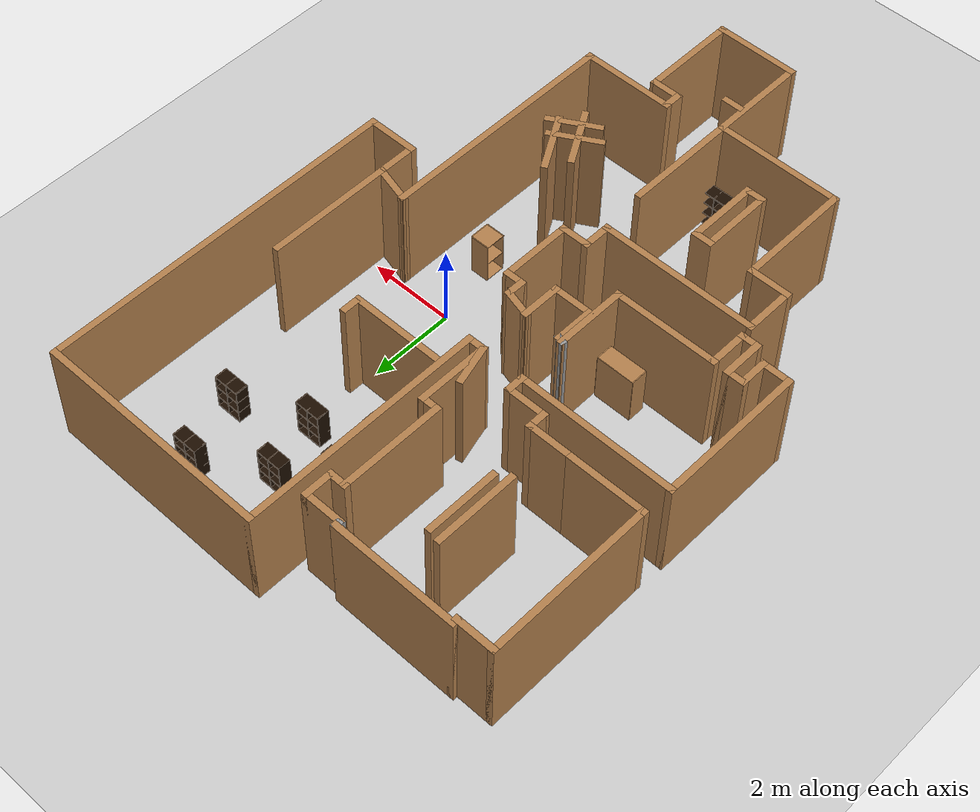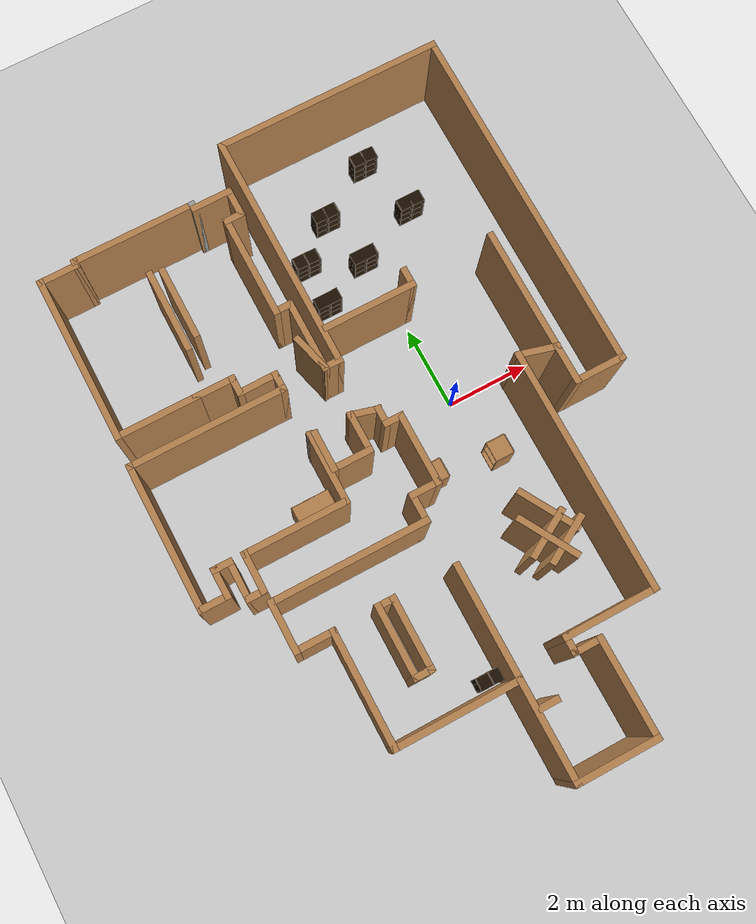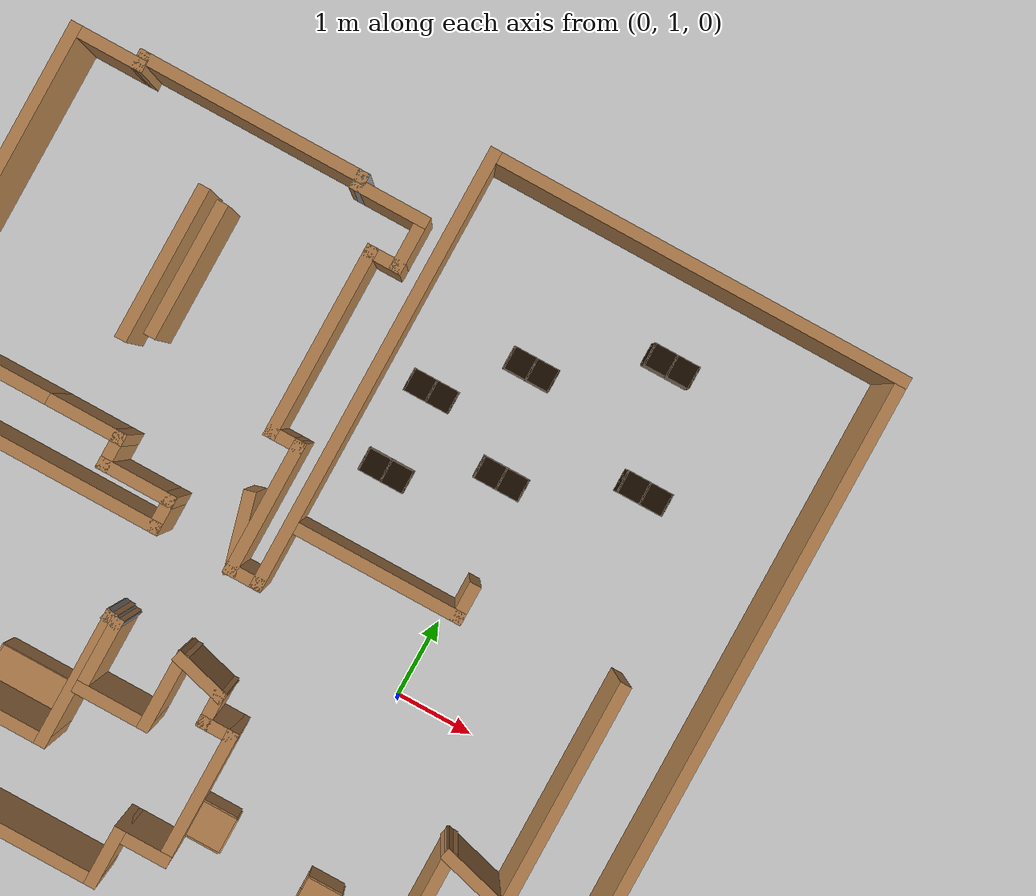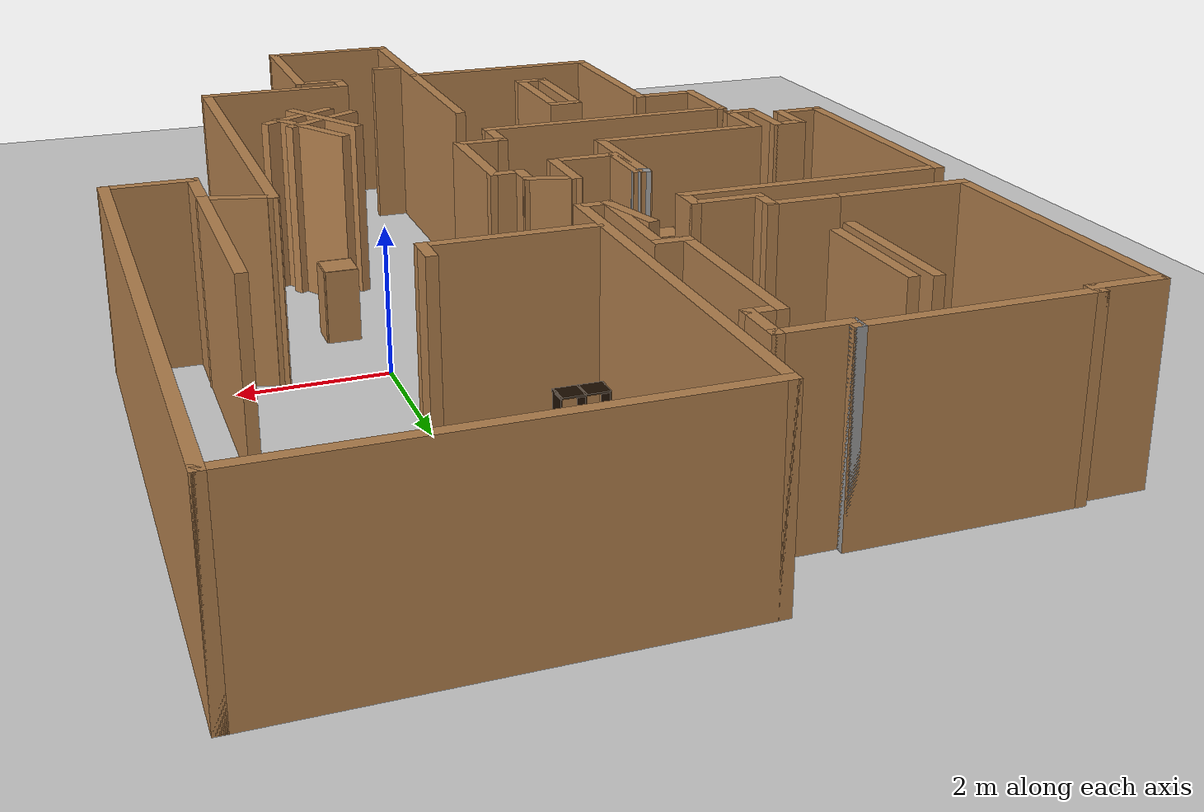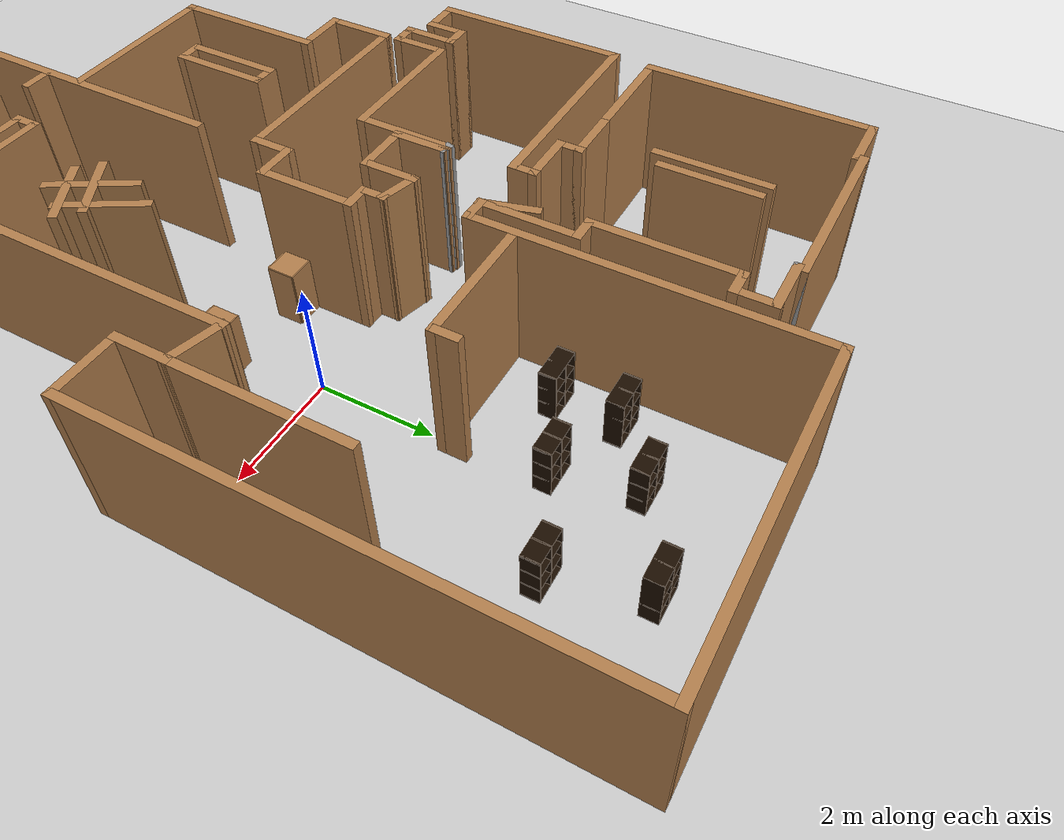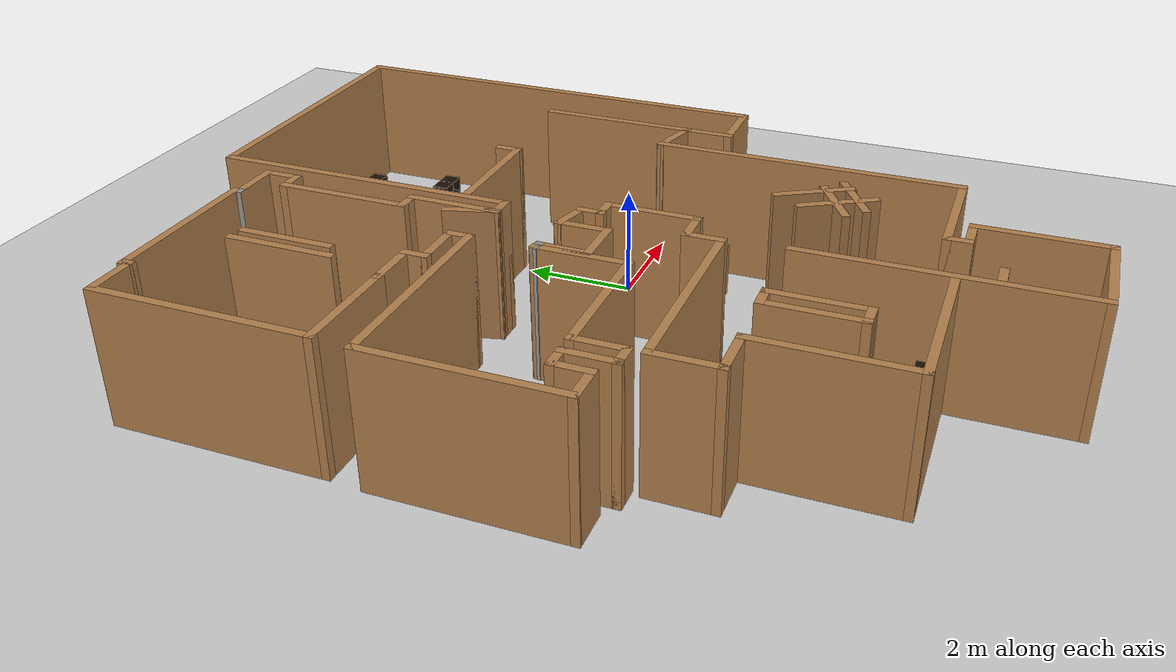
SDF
<sdf version="1.6">
 <world name="default">
  <light name="sun" type="directional">
   <pose>0 0 10 0 -0 0</pose>
   <diffuse>0.8 0.8 0.8 1</diffuse>
   <specular>0.2 0.2 0.2 1</specular>
   <attenuation>
    <range>1000</range>
    <constant>0.9</constant>
    <linear>0.01</linear>
    <quadratic>0.001</quadratic>
   </attenuation>
   <direction>-0.5 0.1 -0.9</direction>
  </light>
  <model name="ground_plane">
   <static>1</static>
   <link name="link">
    <collision name="collision">
     <geometry><plane><normal>0 0 1</normal><size>100 100</size></plane></geometry>
     <surface><friction><ode><mu>100</mu><mu2>50</mu2></ode></friction></surface>
    </collision>
    <visual name="visual">
     <cast_shadows>0</cast_shadows>
     <geometry><plane><normal>0 0 1</normal><size>100 100</size></plane></geometry>
     <material>
      <script><uri>file://media/materials/scripts/gazebo.material</uri><name>Gazebo/Grey</name></script>
     </material>
    </visual>
   </link>
  </model>
  <gravity>0 0 -9.8</gravity>
  <magnetic_field>6e-06 2.3e-05 -4.2e-05</magnetic_field>
  <atmosphere type="adiabatic"/>
  <physics name="default_physics" default="0" type="ode">
   <max_step_size>0.001</max_step_size>
   <real_time_factor>1</real_time_factor>
   <real_time_update_rate>1000</real_time_update_rate>
  </physics>
  <scene><ambient>0.4 0.4 0.4 1</ambient><background>0.7 0.7 0.7 1</background><shadows>1</shadows></scene>
  <spherical_coordinates>
   <surface_model>EARTH_WGS84</surface_model>
   <latitude_deg>0</latitude_deg>
   <longitude_deg>0</longitude_deg>
   <elevation>0</elevation>
   <heading_deg>0</heading_deg>
  </spherical_coordinates>
  <model name="map_19">
   <pose>-1.87689 -0.616254 0 0 -0 0</pose>
   <link name="Wall_0">
    <collision name="Wall_0_Collision">
     <geometry><box><size>2 0.15 2.5</size></box></geometry>
     <pose>0 0 1.25 0 -0 0</pose>
    </collision>
    <visual name="Wall_0_Visual">
     <pose>0 0 1.25 0 -0 0</pose>
     <geometry><box><size>2 0.15 2.5</size></box></geometry>
     <material>
      <script><uri>file://media/materials/scripts/gazebo.material</uri><name>Gazebo/Wood</name></script>
      <ambient>1 1 1 1</ambient>
     </material>
     <meta><layer>0</layer></meta>
    </visual>
    <pose>0.811594 -7.72117 0 0 -0 3.14159</pose>
   </link>
   <link name="Wall_1">
    <collision name="Wall_1_Collision">
     <geometry><box><size>5 0.15 2.5</size></box></geometry>
     <pose>0 0 1.25 0 -0 0</pose>
    </collision>
    <visual name="Wall_1_Visual">
     <pose>0 0 1.25 0 -0 0</pose>
     <geometry><box><size>5 0.15 2.5</size></box></geometry>
     <material>
      <script><uri>file://media/materials/scripts/gazebo.material</uri><name>Gazebo/Wood</name></script>
      <ambient>1 1 1 1</ambient>
     </material>
     <meta><layer>0</layer></meta>
    </visual>
    <pose>-0.113406 -5.29617 0 0 -0 1.5708</pose>
   </link>
   <link name="Wall_10">
    <collision name="Wall_10_Collision">
     <geometry><box><size>0.75 0.15 2.5</size></box></geometry>
     <pose>0 0 1.25 0 -0 0</pose>
    </collision>
    <visual name="Wall_10_Visual">
     <pose>0 0 1.25 0 -0 0</pose>
     <geometry><box><size>0.75 0.15 2.5</size></box></geometry>
     <material>
      <script><uri>file://media/materials/scripts/gazebo.material</uri><name>Gazebo/Wood</name></script>
      <ambient>1 1 1 1</ambient>
     </material>
     <meta><layer>0</layer></meta>
    </visual>
    <pose>-0.223852 -1.45974 0 0 -0 1.5708</pose>
   </link>
   <link name="Wall_11">
    <collision name="Wall_11_Collision">
     <geometry><box><size>0.75 0.15 2.5</size></box></geometry>
     <pose>0 0 1.25 0 -0 0</pose>
    </collision>
    <visual name="Wall_11_Visual">
     <pose>0 0 1.25 0 -0 0</pose>
     <geometry><box><size>0.75 0.15 2.5</size></box></geometry>
     <material>
      <script><uri>file://media/materials/scripts/gazebo.material</uri><name>Gazebo/Wood</name></script>
      <ambient>1 1 1 1</ambient>
     </material>
     <meta><layer>0</layer></meta>
    </visual>
    <pose>0.076148 -1.15974 0 0 -0 0</pose>
   </link>
   <link name="Wall_12">
    <collision name="Wall_12_Collision">
     <geometry><box><size>1.75 0.15 2.5</size></box></geometry>
     <pose>0 0 1.25 0 -0 0</pose>
    </collision>
    <visual name="Wall_12_Visual">
     <pose>0 0 1.25 0 -0 0</pose>
     <geometry><box><size>1.75 0.15 2.5</size></box></geometry>
     <material>
      <script><uri>file://media/materials/scripts/gazebo.material</uri><name>Gazebo/Wood</name></script>
      <ambient>1 1 1 1</ambient>
     </material>
     <meta><layer>0</layer></meta>
    </visual>
    <pose>0.376148 -0.359742 0 0 -0 1.5708</pose>
   </link>
   <link name="Wall_13">
    <collision name="Wall_13_Collision">
     <geometry><box><size>0.5 0.15 2.5</size></box></geometry>
     <pose>0 0 1.25 0 -0 0</pose>
    </collision>
    <visual name="Wall_13_Visual">
     <pose>0 0 1.25 0 -0 0</pose>
     <geometry><box><size>0.5 0.15 2.5</size></box></geometry>
     <material>
      <script><uri>file://media/materials/scripts/gazebo.material</uri><name>Gazebo/Wood</name></script>
      <ambient>1 1 1 1</ambient>
     </material>
     <meta><layer>0</layer></meta>
    </visual>
    <pose>0.201148 0.440258 0 0 -0 3.14159</pose>
   </link>
   <link name="Wall_14">
    <collision name="Wall_14_Collision">
     <geometry><box><size>0.5 0.15 2.5</size></box></geometry>
     <pose>0 0 1.25 0 -0 0</pose>
    </collision>
    <visual name="Wall_14_Visual">
     <pose>0 0 1.25 0 -0 0</pose>
     <geometry><box><size>0.5 0.15 2.5</size></box></geometry>
     <material>
      <script><uri>file://media/materials/scripts/gazebo.material</uri><name>Gazebo/Wood</name></script>
      <ambient>1 1 1 1</ambient>
     </material>
     <meta><layer>0</layer></meta>
    </visual>
    <pose>0.026148 0.615258 0 0 -0 1.5708</pose>
   </link>
   <link name="Wall_15">
    <collision name="Wall_15_Collision">
     <geometry><box><size>0.75 0.15 2.5</size></box></geometry>
     <pose>0 0 1.25 0 -0 0</pose>
    </collision>
    <visual name="Wall_15_Visual">
     <pose>0 0 1.25 0 -0 0</pose>
     <geometry><box><size>0.75 0.15 2.5</size></box></geometry>
     <material>
      <script><uri>file://media/materials/scripts/gazebo.material</uri><name>Gazebo/Wood</name></script>
      <ambient>1 1 1 1</ambient>
     </material>
     <meta><layer>0</layer></meta>
    </visual>
    <pose>-0.26363 0.867903 0 0 -0 2.87979</pose>
   </link>
   <link name="Wall_16">
    <collision name="Wall_16_Collision">
     <geometry><box><size>1 0.15 2.5</size></box></geometry>
     <pose>0 0 1.25 0 -0 0</pose>
    </collision>
    <visual name="Wall_16_Visual">
     <pose>0 0 1.25 0 -0 0</pose>
     <geometry><box><size>1 0.15 2.5</size></box></geometry>
     <material>
      <script><uri>file://media/materials/scripts/gazebo.material</uri><name>Gazebo/Wood</name></script>
      <ambient>1 1 1 1</ambient>
     </material>
     <meta><layer>0</layer></meta>
    </visual>
    <pose>-0.553407 0.520549 0 0 -0 -1.5708</pose>
   </link>
   <link name="Wall_17">
    <collision name="Wall_17_Collision">
     <geometry><box><size>1 0.15 2.5</size></box></geometry>
     <pose>0 0 1.25 0 -0 0</pose>
    </collision>
    <visual name="Wall_17_Visual">
     <pose>0 0 1.25 0 -0 0</pose>
     <geometry><box><size>1 0.15 2.5</size></box></geometry>
     <material>
      <script><uri>file://media/materials/scripts/gazebo.material</uri><name>Gazebo/Wood</name></script>
      <ambient>1 1 1 1</ambient>
     </material>
     <meta><layer>0</layer></meta>
    </visual>
    <pose>-0.978407 0.095549 0 0 -0 3.14159</pose>
   </link>
   <link name="Wall_18">
    <collision name="Wall_18_Collision">
     <geometry><box><size>1 0.15 2.5</size></box></geometry>
     <pose>0 0 1.25 0 -0 0</pose>
    </collision>
    <visual name="Wall_18_Visual">
     <pose>0 0 1.25 0 -0 0</pose>
     <geometry><box><size>1 0.15 2.5</size></box></geometry>
     <material>
      <script><uri>file://media/materials/scripts/gazebo.material</uri><name>Gazebo/Wood</name></script>
      <ambient>1 1 1 1</ambient>
     </material>
     <meta><layer>0</layer></meta>
    </visual>
    <pose>-1.40341 0.520549 0 0 -0 1.5708</pose>
   </link>
   <link name="Wall_19">
    <collision name="Wall_19_Collision">
     <geometry><box><size>0.25 0.15 2.5</size></box></geometry>
     <pose>0 0 1.25 0 -0 0</pose>
    </collision>
    <visual name="Wall_19_Visual">
     <pose>0 0 1.25 0 -0 0</pose>
     <geometry><box><size>0.25 0.15 2.5</size></box></geometry>
     <material>
      <script><uri>file://media/materials/scripts/gazebo.material</uri><name>Gazebo/Grey</name></script>
      <ambient>1 1 1 1</ambient>
     </material>
     <meta><layer>0</layer></meta>
    </visual>
    <pose>-1.4517 0.95849 0 0 -0 2.87979</pose>
   </link>
   <link name="Wall_20">
    <collision name="Wall_20_Collision">
     <geometry><box><size>1.75 0.15 2.5</size></box></geometry>
     <pose>0 0 1.25 0 -0 0</pose>
    </collision>
    <visual name="Wall_20_Visual">
     <pose>0 0 1.25 0 -0 0</pose>
     <geometry><box><size>1.75 0.15 2.5</size></box></geometry>
     <material>
      <script><uri>file://media/materials/scripts/gazebo.material</uri><name>Gazebo/Wood</name></script>
      <ambient>1 1 1 1</ambient>
     </material>
     <meta><layer>0</layer></meta>
    </visual>
    <pose>-1.5 0.171431 0 0 -0 -1.5708</pose>
   </link>
   <link name="Wall_21">
    <collision name="Wall_21_Collision">
     <geometry><box><size>2.5 0.15 2.5</size></box></geometry>
     <pose>0 0 1.25 0 -0 0</pose>
    </collision>
    <visual name="Wall_21_Visual">
     <pose>0 0 1.25 0 -0 0</pose>
     <geometry><box><size>2.5 0.15 2.5</size></box></geometry>
     <material>
      <script><uri>file://media/materials/scripts/gazebo.material</uri><name>Gazebo/Wood</name></script>
      <ambient>1 1 1 1</ambient>
     </material>
     <meta><layer>0</layer></meta>
    </visual>
    <pose>-2.675 -0.628569 0 0 -0 3.14159</pose>
   </link>
   <link name="Wall_22">
    <collision name="Wall_22_Collision">
     <geometry><box><size>1 0.15 2.5</size></box></geometry>
     <pose>0 0 1.25 0 -0 0</pose>
    </collision>
    <visual name="Wall_22_Visual">
     <pose>0 0 1.25 0 -0 0</pose>
     <geometry><box><size>1 0.15 2.5</size></box></geometry>
     <material>
      <script><uri>file://media/materials/scripts/gazebo.material</uri><name>Gazebo/Wood</name></script>
      <ambient>1 1 1 1</ambient>
     </material>
     <meta><layer>0</layer></meta>
    </visual>
    <pose>-3.85 -1.05357 0 0 -0 -1.5708</pose>
   </link>
   <link name="Wall_23">
    <collision name="Wall_23_Collision">
     <geometry><box><size>0.5 0.15 2.5</size></box></geometry>
     <pose>0 0 1.25 0 -0 0</pose>
    </collision>
    <visual name="Wall_23_Visual">
     <pose>0 0 1.25 0 -0 0</pose>
     <geometry><box><size>0.5 0.15 2.5</size></box></geometry>
     <material>
      <script><uri>file://media/materials/scripts/gazebo.material</uri><name>Gazebo/Wood</name></script>
      <ambient>1 1 1 1</ambient>
     </material>
     <meta><layer>0</layer></meta>
    </visual>
    <pose>-4.025 -1.47857 0 0 -0 3.14159</pose>
   </link>
   <link name="Wall_24">
    <collision name="Wall_24_Collision">
     <geometry><box><size>1 0.15 2.5</size></box></geometry>
     <pose>0 0 1.25 0 -0 0</pose>
    </collision>
    <visual name="Wall_24_Visual">
     <pose>0 0 1.25 0 -0 0</pose>
     <geometry><box><size>1 0.15 2.5</size></box></geometry>
     <material>
      <script><uri>file://media/materials/scripts/gazebo.material</uri><name>Gazebo/Wood</name></script>
      <ambient>1 1 1 1</ambient>
     </material>
     <meta><layer>0</layer></meta>
    </visual>
    <pose>-4.2 -1.05357 0 0 -0 1.5708</pose>
   </link>
   <link name="Wall_25">
    <collision name="Wall_25_Collision">
     <geometry><box><size>0.5 0.15 2.5</size></box></geometry>
     <pose>0 0 1.25 0 -0 0</pose>
    </collision>
    <visual name="Wall_25_Visual">
     <pose>0 0 1.25 0 -0 0</pose>
     <geometry><box><size>0.5 0.15 2.5</size></box></geometry>
     <material>
      <script><uri>file://media/materials/scripts/gazebo.material</uri><name>Gazebo/Wood</name></script>
      <ambient>1 1 1 1</ambient>
     </material>
     <meta><layer>0</layer></meta>
    </visual>
    <pose>-4.375 -0.628569 0 0 -0 3.14159</pose>
   </link>
   <link name="Wall_26">
    <collision name="Wall_26_Collision">
     <geometry><box><size>0.75 0.15 2.5</size></box></geometry>
     <pose>0 0 1.25 0 -0 0</pose>
    </collision>
    <visual name="Wall_26_Visual">
     <pose>0 0 1.25 0 -0 0</pose>
     <geometry><box><size>0.75 0.15 2.5</size></box></geometry>
     <material>
      <script><uri>file://media/materials/scripts/gazebo.material</uri><name>Gazebo/Wood</name></script>
      <ambient>1 1 1 1</ambient>
     </material>
     <meta><layer>0</layer></meta>
    </visual>
    <pose>-4.55 -0.928569 0 0 -0 -1.5708</pose>
   </link>
   <link name="Wall_27">
    <collision name="Wall_27_Collision">
     <geometry><box><size>0.75 0.15 2.5</size></box></geometry>
     <pose>0 0 1.25 0 -0 0</pose>
    </collision>
    <visual name="Wall_27_Visual">
     <pose>0 0 1.25 0 -0 0</pose>
     <geometry><box><size>0.75 0.15 2.5</size></box></geometry>
     <material>
      <script><uri>file://media/materials/scripts/gazebo.material</uri><name>Gazebo/Wood</name></script>
      <ambient>1 1 1 1</ambient>
     </material>
     <meta><layer>0</layer></meta>
    </visual>
    <pose>-4.85 -1.22857 0 0 -0 3.14159</pose>
   </link>
   <link name="Wall_28">
    <collision name="Wall_28_Collision">
     <geometry><box><size>3.5 0.15 2.5</size></box></geometry>
     <pose>0 0 1.25 0 -0 0</pose>
    </collision>
    <visual name="Wall_28_Visual">
     <pose>0 0 1.25 0 -0 0</pose>
     <geometry><box><size>3.5 0.15 2.5</size></box></geometry>
     <material>
      <script><uri>file://media/materials/scripts/gazebo.material</uri><name>Gazebo/Wood</name></script>
      <ambient>1 1 1 1</ambient>
     </material>
     <meta><layer>0</layer></meta>
    </visual>
    <pose>-5.15 0.446431 0 0 -0 1.5708</pose>
   </link>
   <link name="Wall_29">
    <collision name="Wall_29_Collision">
     <geometry><box><size>3.75 0.15 2.5</size></box></geometry>
     <pose>0 0 1.25 0 -0 0</pose>
    </collision>
    <visual name="Wall_29_Visual">
     <pose>0 0 1.25 0 -0 0</pose>
     <geometry><box><size>3.75 0.15 2.5</size></box></geometry>
     <material>
      <script><uri>file://media/materials/scripts/gazebo.material</uri><name>Gazebo/Wood</name></script>
      <ambient>1 1 1 1</ambient>
     </material>
     <meta><layer>0</layer></meta>
    </visual>
    <pose>-3.35 2.12143 0 0 -0 0</pose>
   </link>
   <link name="Wall_3">
    <collision name="Wall_3_Collision">
     <geometry><box><size>0.5 0.15 2.5</size></box></geometry>
     <pose>0 0 1.25 0 -0 0</pose>
    </collision>
    <visual name="Wall_3_Visual">
     <pose>0 0 1.25 0 -0 0</pose>
     <geometry><box><size>0.5 0.15 2.5</size></box></geometry>
     <material>
      <script><uri>file://media/materials/scripts/gazebo.material</uri><name>Gazebo/Wood</name></script>
      <ambient>1 1 1 1</ambient>
     </material>
     <meta><layer>0</layer></meta>
    </visual>
    <pose>0.160001 -6.13273 0 0 -0 3.14159</pose>
   </link>
   <link name="Wall_31">
    <collision name="Wall_31_Collision">
     <geometry><box><size>0.5 0.15 2.5</size></box></geometry>
     <pose>0 0 1.25 0 -0 0</pose>
    </collision>
    <visual name="Wall_31_Visual">
     <pose>0 0 1.25 0 -0 0</pose>
     <geometry><box><size>0.5 0.15 2.5</size></box></geometry>
     <material>
      <script><uri>file://media/materials/scripts/gazebo.material</uri><name>Gazebo/Wood</name></script>
      <ambient>1 1 1 1</ambient>
     </material>
     <meta><layer>0</layer></meta>
    </visual>
    <pose>-1.55 2.29643 0 0 -0 1.5708</pose>
   </link>
   <link name="Wall_32">
    <collision name="Wall_32_Collision">
     <geometry><box><size>1 0.15 2.5</size></box></geometry>
     <pose>0 0 1.25 0 -0 0</pose>
    </collision>
    <visual name="Wall_32_Visual">
     <pose>0 0 1.25 0 -0 0</pose>
     <geometry><box><size>1 0.15 2.5</size></box></geometry>
     <material>
      <script><uri>file://media/materials/scripts/gazebo.material</uri><name>Gazebo/Wood</name></script>
      <ambient>1 1 1 1</ambient>
     </material>
     <meta><layer>0</layer></meta>
    </visual>
    <pose>-1.975 2.47143 0 0 -0 3.14159</pose>
   </link>
   <link name="Wall_33">
    <collision name="Wall_33_Collision">
     <geometry><box><size>0.5 0.15 2.5</size></box></geometry>
     <pose>0 0 1.25 0 -0 0</pose>
    </collision>
    <visual name="Wall_33_Visual">
     <pose>0 0 1.25 0 -0 0</pose>
     <geometry><box><size>0.5 0.15 2.5</size></box></geometry>
     <material>
      <script><uri>file://media/materials/scripts/gazebo.material</uri><name>Gazebo/Wood</name></script>
      <ambient>1 1 1 1</ambient>
     </material>
     <meta><layer>0</layer></meta>
    </visual>
    <pose>-2.4 2.64643 0 0 -0 1.5708</pose>
   </link>
   <link name="Wall_34">
    <collision name="Wall_34_Collision">
     <geometry><box><size>1 0.15 2.5</size></box></geometry>
     <pose>0 0 1.25 0 -0 0</pose>
    </collision>
    <visual name="Wall_34_Visual">
     <pose>0 0 1.25 0 -0 0</pose>
     <geometry><box><size>1 0.15 2.5</size></box></geometry>
     <material>
      <script><uri>file://media/materials/scripts/gazebo.material</uri><name>Gazebo/Wood</name></script>
      <ambient>1 1 1 1</ambient>
     </material>
     <meta><layer>0</layer></meta>
    </visual>
    <pose>-2.825 2.82143 0 0 -0 3.14159</pose>
   </link>
   <link name="Wall_35">
    <collision name="Wall_35_Collision">
     <geometry><box><size>2 0.15 2.5</size></box></geometry>
     <pose>0 0 1.25 0 -0 0</pose>
    </collision>
    <visual name="Wall_35_Visual">
     <pose>0 0 1.25 0 -0 0</pose>
     <geometry><box><size>2 0.15 2.5</size></box></geometry>
     <material>
      <script><uri>file://media/materials/scripts/gazebo.material</uri><name>Gazebo/Wood</name></script>
      <ambient>1 1 1 1</ambient>
     </material>
     <meta><layer>0</layer></meta>
    </visual>
    <pose>-4.175 2.82143 0 0 -0 3.14159</pose>
   </link>
   <link name="Wall_36">
    <collision name="Wall_36_Collision">
     <geometry><box><size>4 0.15 2.5</size></box></geometry>
     <pose>0 0 1.25 0 -0 0</pose>
    </collision>
    <visual name="Wall_36_Visual">
     <pose>0 0 1.25 0 -0 0</pose>
     <geometry><box><size>4 0.15 2.5</size></box></geometry>
     <material>
      <script><uri>file://media/materials/scripts/gazebo.material</uri><name>Gazebo/Wood</name></script>
      <ambient>1 1 1 1</ambient>
     </material>
     <meta><layer>0</layer></meta>
    </visual>
    <pose>-5.1 4.74643 0 0 -0 1.5708</pose>
   </link>
   <link name="Wall_37">
    <collision name="Wall_37_Collision">
     <geometry><box><size>1 0.15 2.5</size></box></geometry>
     <pose>0 0 1.25 0 -0 0</pose>
    </collision>
    <visual name="Wall_37_Visual">
     <pose>0 0 1.25 0 -0 0</pose>
     <geometry><box><size>1 0.15 2.5</size></box></geometry>
     <material>
      <script><uri>file://media/materials/scripts/gazebo.material</uri><name>Gazebo/Wood</name></script>
      <ambient>1 1 1 1</ambient>
     </material>
     <meta><layer>0</layer></meta>
    </visual>
    <pose>-4.675 6.67143 0 0 -0 0</pose>
   </link>
   <link name="Wall_39">
    <collision name="Wall_39_Collision">
     <geometry><box><size>0.25 0.15 2.5</size></box></geometry>
     <pose>0 0 1.25 0 -0 0</pose>
    </collision>
    <visual name="Wall_39_Visual">
     <pose>0 0 1.25 0 -0 0</pose>
     <geometry><box><size>0.25 0.15 2.5</size></box></geometry>
     <material>
      <script><uri>file://media/materials/scripts/gazebo.material</uri><name>Gazebo/Wood</name></script>
      <ambient>1 1 1 1</ambient>
     </material>
     <meta><layer>0</layer></meta>
    </visual>
    <pose>-4.25 6.72143 0 0 -0 1.5708</pose>
   </link>
   <link name="Wall_40">
    <collision name="Wall_40_Collision">
     <geometry><box><size>3 0.15 2.5</size></box></geometry>
     <pose>0 0 1.25 0 -0 0</pose>
    </collision>
    <visual name="Wall_40_Visual">
     <pose>0 0 1.25 0 -0 0</pose>
     <geometry><box><size>3 0.15 2.5</size></box></geometry>
     <material>
      <script><uri>file://media/materials/scripts/gazebo.material</uri><name>Gazebo/Wood</name></script>
      <ambient>1 1 1 1</ambient>
     </material>
     <meta><layer>0</layer></meta>
    </visual>
    <pose>-2.825 6.77143 0 0 -0 0</pose>
   </link>
   <link name="Wall_41">
    <collision name="Wall_41_Collision">
     <geometry><box><size>0.25 0.15 2.5</size></box></geometry>
     <pose>0 0 1.25 0 -0 0</pose>
    </collision>
    <visual name="Wall_41_Visual">
     <pose>0 0 1.25 0 -0 0</pose>
     <geometry><box><size>0.25 0.15 2.5</size></box></geometry>
     <material>
      <script><uri>file://media/materials/scripts/gazebo.material</uri><name>Gazebo/Grey</name></script>
      <ambient>1 1 1 1</ambient>
     </material>
     <meta><layer>0</layer></meta>
    </visual>
    <pose>-1.4 6.72143 0 0 -0 -1.5708</pose>
   </link>
   <link name="Wall_42">
    <collision name="Wall_42_Collision">
     <geometry><box><size>1 0.15 2.5</size></box></geometry>
     <pose>0 0 1.25 0 -0 0</pose>
    </collision>
    <visual name="Wall_42_Visual">
     <pose>0 0 1.25 0 -0 0</pose>
     <geometry><box><size>1 0.15 2.5</size></box></geometry>
     <material>
      <script><uri>file://media/materials/scripts/gazebo.material</uri><name>Gazebo/Wood</name></script>
      <ambient>1 1 1 1</ambient>
     </material>
     <meta><layer>0</layer></meta>
    </visual>
    <pose>-0.975 6.67143 0 0 -0 0</pose>
   </link>
   <link name="Wall_43">
    <collision name="Wall_43_Collision">
     <geometry><box><size>0.75 0.15 2.5</size></box></geometry>
     <pose>0 0 1.25 0 -0 0</pose>
    </collision>
    <visual name="Wall_43_Visual">
     <pose>0 0 1.25 0 -0 0</pose>
     <geometry><box><size>0.75 0.15 2.5</size></box></geometry>
     <material>
      <script><uri>file://media/materials/scripts/gazebo.material</uri><name>Gazebo/Wood</name></script>
      <ambient>1 1 1 1</ambient>
     </material>
     <meta><layer>0</layer></meta>
    </visual>
    <pose>-0.55 6.37143 0 0 -0 -1.5708</pose>
   </link>
   <link name="Wall_44">
    <collision name="Wall_44_Collision">
     <geometry><box><size>0.5 0.15 2.5</size></box></geometry>
     <pose>0 0 1.25 0 -0 0</pose>
    </collision>
    <visual name="Wall_44_Visual">
     <pose>0 0 1.25 0 -0 0</pose>
     <geometry><box><size>0.5 0.15 2.5</size></box></geometry>
     <material>
      <script><uri>file://media/materials/scripts/gazebo.material</uri><name>Gazebo/Wood</name></script>
      <ambient>1 1 1 1</ambient>
     </material>
     <meta><layer>0</layer></meta>
    </visual>
    <pose>-0.725 6.07143 0 0 -0 3.14159</pose>
   </link>
   <link name="Wall_45">
    <collision name="Wall_45_Collision">
     <geometry><box><size>2.5 0.15 2.5</size></box></geometry>
     <pose>0 0 1.25 0 -0 0</pose>
    </collision>
    <visual name="Wall_45_Visual">
     <pose>0 0 1.25 0 -0 0</pose>
     <geometry><box><size>2.5 0.15 2.5</size></box></geometry>
     <material>
      <script><uri>file://media/materials/scripts/gazebo.material</uri><name>Gazebo/Wood</name></script>
      <ambient>1 1 1 1</ambient>
     </material>
     <meta><layer>0</layer></meta>
    </visual>
    <pose>-0.9 4.89643 0 0 -0 -1.5708</pose>
   </link>
   <link name="Wall_46">
    <collision name="Wall_46_Collision">
     <geometry><box><size>0.5 0.15 2.5</size></box></geometry>
     <pose>0 0 1.25 0 -0 0</pose>
    </collision>
    <visual name="Wall_46_Visual">
     <pose>0 0 1.25 0 -0 0</pose>
     <geometry><box><size>0.5 0.15 2.5</size></box></geometry>
     <material>
      <script><uri>file://media/materials/scripts/gazebo.material</uri><name>Gazebo/Wood</name></script>
      <ambient>1 1 1 1</ambient>
     </material>
     <meta><layer>0</layer></meta>
    </visual>
    <pose>-0.725 3.72143 0 0 -0 0</pose>
   </link>
   <link name="Wall_47">
    <collision name="Wall_47_Collision">
     <geometry><box><size>1.75 0.15 2.5</size></box></geometry>
     <pose>0 0 1.25 0 -0 0</pose>
    </collision>
    <visual name="Wall_47_Visual">
     <pose>0 0 1.25 0 -0 0</pose>
     <geometry><box><size>1.75 0.15 2.5</size></box></geometry>
     <material>
      <script><uri>file://media/materials/scripts/gazebo.material</uri><name>Gazebo/Wood</name></script>
      <ambient>1 1 1 1</ambient>
     </material>
     <meta><layer>0</layer></meta>
    </visual>
    <pose>-0.55 2.92143 0 0 -0 -1.5708</pose>
   </link>
   <link name="Wall_48">
    <collision name="Wall_48_Collision">
     <geometry><box><size>1 0.15 2.5</size></box></geometry>
     <pose>0 0 1.25 0 -0 0</pose>
    </collision>
    <visual name="Wall_48_Visual">
     <pose>0 0 1.25 0 -0 0</pose>
     <geometry><box><size>1 0.15 2.5</size></box></geometry>
     <material>
      <script><uri>file://media/materials/scripts/gazebo.material</uri><name>Gazebo/Wood</name></script>
      <ambient>1 1 1 1</ambient>
     </material>
     <meta><layer>0</layer></meta>
    </visual>
    <pose>-0.659998 2.53195 0 0 -0 1.8326</pose>
   </link>
   <link name="Wall_5">
    <collision name="Wall_5_Collision">
     <geometry><box><size>3 0.15 2.5</size></box></geometry>
     <pose>0 0 1.25 0 -0 0</pose>
    </collision>
    <visual name="Wall_5_Visual">
     <pose>0 0 1.25 0 -0 0</pose>
     <geometry><box><size>3 0.15 2.5</size></box></geometry>
     <material>
      <script><uri>file://media/materials/scripts/gazebo.material</uri><name>Gazebo/Wood</name></script>
      <ambient>1 1 1 1</ambient>
     </material>
     <meta><layer>0</layer></meta>
    </visual>
    <pose>-1.54885 -5.45974 0 0 -0 3.14159</pose>
   </link>
   <link name="Wall_50">
    <collision name="Wall_50_Collision">
     <geometry><box><size>0.5 0.15 2.5</size></box></geometry>
     <pose>0 0 1.25 0 -0 0</pose>
    </collision>
    <visual name="Wall_50_Visual">
     <pose>0 0 1.25 0 -0 0</pose>
     <geometry><box><size>0.5 0.15 2.5</size></box></geometry>
     <material>
      <script><uri>file://media/materials/scripts/gazebo.material</uri><name>Gazebo/Wood</name></script>
      <ambient>1 1 1 1</ambient>
     </material>
     <meta><layer>0</layer></meta>
    </visual>
    <pose>-0.375 2.12143 0 0 -0 0</pose>
   </link>
   <link name="Wall_53">
    <collision name="Wall_53_Collision">
     <geometry><box><size>5.75 0.15 2.5</size></box></geometry>
     <pose>0 0 1.25 0 -0 0</pose>
    </collision>
    <visual name="Wall_53_Visual">
     <pose>0 0 1.25 0 -0 0</pose>
     <geometry><box><size>5.75 0.15 2.5</size></box></geometry>
     <material>
      <script><uri>file://media/materials/scripts/gazebo.material</uri><name>Gazebo/Wood</name></script>
      <ambient>1 1 1 1</ambient>
     </material>
     <meta><layer>0</layer></meta>
    </visual>
    <pose>-0.2 4.92143 0 0 -0 1.5708</pose>
   </link>
   <link name="Wall_54">
    <collision name="Wall_54_Collision">
     <geometry><box><size>5.5 0.15 2.5</size></box></geometry>
     <pose>0 0 1.25 0 -0 0</pose>
    </collision>
    <visual name="Wall_54_Visual">
     <pose>0 0 1.25 0 -0 0</pose>
     <geometry><box><size>5.5 0.15 2.5</size></box></geometry>
     <material>
      <script><uri>file://media/materials/scripts/gazebo.material</uri><name>Gazebo/Wood</name></script>
      <ambient>1 1 1 1</ambient>
     </material>
     <meta><layer>0</layer></meta>
    </visual>
    <pose>2.475 7.72143 0 0 -0 0</pose>
   </link>
   <link name="Wall_56">
    <collision name="Wall_56_Collision">
     <geometry><box><size>8.5 0.15 2.5</size></box></geometry>
     <pose>0 0 1.25 0 -0 0</pose>
    </collision>
    <visual name="Wall_56_Visual">
     <pose>0 0 1.25 0 -0 0</pose>
     <geometry><box><size>8.5 0.15 2.5</size></box></geometry>
     <material>
      <script><uri>file://media/materials/scripts/gazebo.material</uri><name>Gazebo/Wood</name></script>
      <ambient>1 1 1 1</ambient>
     </material>
     <meta><layer>0</layer></meta>
    </visual>
    <pose>5.15 3.54643 0 0 -0 -1.5708</pose>
   </link>
   <link name="Wall_57">
    <collision name="Wall_57_Collision">
     <geometry><box><size>1.25 0.15 2.5</size></box></geometry>
     <pose>0 0 1.25 0 -0 0</pose>
    </collision>
    <visual name="Wall_57_Visual">
     <pose>0 0 1.25 0 -0 0</pose>
     <geometry><box><size>1.25 0.15 2.5</size></box></geometry>
     <material>
      <script><uri>file://media/materials/scripts/gazebo.material</uri><name>Gazebo/Wood</name></script>
      <ambient>1 1 1 1</ambient>
     </material>
     <meta><layer>0</layer></meta>
    </visual>
    <pose>4.6 -0.628569 0 0 -0 3.14159</pose>
   </link>
   <link name="Wall_58">
    <collision name="Wall_58_Collision">
     <geometry><box><size>1 0.15 2.5</size></box></geometry>
     <pose>0 0 1.25 0 -0 0</pose>
    </collision>
    <visual name="Wall_58_Visual">
     <pose>0 0 1.25 0 -0 0</pose>
     <geometry><box><size>1 0.15 2.5</size></box></geometry>
     <material>
      <script><uri>file://media/materials/scripts/gazebo.material</uri><name>Gazebo/Wood</name></script>
      <ambient>1 1 1 1</ambient>
     </material>
     <meta><layer>0</layer></meta>
    </visual>
    <pose>4.05 -0.203569 0 0 -0 1.5708</pose>
   </link>
   <link name="Wall_59">
    <collision name="Wall_59_Collision">
     <geometry><box><size>1 0.15 2.5</size></box></geometry>
     <pose>0 0 1.25 0 -0 0</pose>
    </collision>
    <visual name="Wall_59_Visual">
     <pose>0 0 1.25 0 -0 0</pose>
     <geometry><box><size>1 0.15 2.5</size></box></geometry>
     <material>
      <script><uri>file://media/materials/scripts/gazebo.material</uri><name>Gazebo/Wood</name></script>
      <ambient>1 1 1 1</ambient>
     </material>
     <meta><layer>0</layer></meta>
    </visual>
    <pose>3.63948 0.331429 0 0 -0 2.87979</pose>
   </link>
   <link name="Wall_6">
    <collision name="Wall_6_Collision">
     <geometry><box><size>2.75 0.15 2.5</size></box></geometry>
     <pose>0 0 1.25 0 -0 0</pose>
    </collision>
    <visual name="Wall_6_Visual">
     <pose>0 0 1.25 0 -0 0</pose>
     <geometry><box><size>2.75 0.15 2.5</size></box></geometry>
     <material>
      <script><uri>file://media/materials/scripts/gazebo.material</uri><name>Gazebo/Wood</name></script>
      <ambient>1 1 1 1</ambient>
     </material>
     <meta><layer>0</layer></meta>
    </visual>
    <pose>-2.97385 -4.15974 0 0 -0 1.5708</pose>
   </link>
   <link name="Wall_60">
    <collision name="Wall_60_Collision">
     <geometry><box><size>5.75 0.15 2.5</size></box></geometry>
     <pose>0 0 1.25 0 -0 0</pose>
    </collision>
    <visual name="Wall_60_Visual">
     <pose>0 0 1.25 0 -0 0</pose>
     <geometry><box><size>5.75 0.15 2.5</size></box></geometry>
     <material>
      <script><uri>file://media/materials/scripts/gazebo.material</uri><name>Gazebo/Wood</name></script>
      <ambient>1 1 1 1</ambient>
     </material>
     <meta><layer>0</layer></meta>
    </visual>
    <pose>3.22896 -2.35857 0 0 -0 -1.5708</pose>
   </link>
   <link name="Wall_62">
    <collision name="Wall_62_Collision">
     <geometry><box><size>2.25 0.15 2.5</size></box></geometry>
     <pose>0 0 1.25 0 -0 0</pose>
    </collision>
    <visual name="Wall_62_Visual">
     <pose>0 0 1.25 0 -0 0</pose>
     <geometry><box><size>2.25 0.15 2.5</size></box></geometry>
     <material>
      <script><uri>file://media/materials/scripts/gazebo.material</uri><name>Gazebo/Wood</name></script>
      <ambient>1 1 1 1</ambient>
     </material>
     <meta><layer>0</layer></meta>
    </visual>
    <pose>2.17896 -5.15857 0 0 -0 3.14159</pose>
   </link>
   <link name="Wall_63">
    <collision name="Wall_63_Collision">
     <geometry><box><size>0.5 0.15 2.5</size></box></geometry>
     <pose>0 0 1.25 0 -0 0</pose>
    </collision>
    <visual name="Wall_63_Visual">
     <pose>0 0 1.25 0 -0 0</pose>
     <geometry><box><size>0.5 0.15 2.5</size></box></geometry>
     <material>
      <script><uri>file://media/materials/scripts/gazebo.material</uri><name>Gazebo/Wood</name></script>
      <ambient>1 1 1 1</ambient>
     </material>
     <meta><layer>0</layer></meta>
    </visual>
    <pose>1.12896 -5.33357 0 0 -0 -1.5708</pose>
   </link>
   <link name="Wall_64">
    <collision name="Wall_64_Collision">
     <geometry><box><size>0.75 0.15 2.5</size></box></geometry>
     <pose>0 0 1.25 0 -0 0</pose>
    </collision>
    <visual name="Wall_64_Visual">
     <pose>0 0 1.25 0 -0 0</pose>
     <geometry><box><size>0.75 0.15 2.5</size></box></geometry>
     <material>
      <script><uri>file://media/materials/scripts/gazebo.material</uri><name>Gazebo/Wood</name></script>
      <ambient>1 1 1 1</ambient>
     </material>
     <meta><layer>0</layer></meta>
    </visual>
    <pose>1.42896 -5.50857 0 0 -0 0</pose>
   </link>
   <link name="Wall_65">
    <collision name="Wall_65_Collision">
     <geometry><box><size>2.36261 0.15 2.5</size></box></geometry>
     <pose>0 0 1.25 0 -0 0</pose>
    </collision>
    <visual name="Wall_65_Visual">
     <pose>0 0 1.25 0 -0 0</pose>
     <geometry><box><size>2.36261 0.15 2.5</size></box></geometry>
     <material>
      <script><uri>file://media/materials/scripts/gazebo.material</uri><name>Gazebo/Wood</name></script>
      <ambient>1 1 1 1</ambient>
     </material>
     <meta><layer>0</layer></meta>
    </visual>
    <pose>1.73278 -6.61487 0 0 -0 -1.56735</pose>
   </link>
   <link name="Wall_67">
    <collision name="Wall_67_Collision">
     <geometry><box><size>0.5 0.15 2.5</size></box></geometry>
     <pose>0 0 1.25 0 -0 0</pose>
    </collision>
    <visual name="Wall_67_Visual">
     <pose>0 0 1.25 0 -0 0</pose>
     <geometry><box><size>0.5 0.15 2.5</size></box></geometry>
     <material>
      <script><uri>file://media/materials/scripts/gazebo.material</uri><name>Gazebo/Wood</name></script>
      <ambient>1 1 1 1</ambient>
     </material>
     <meta><layer>0</layer></meta>
    </visual>
    <pose>-1.76031 -2.84872 0 0 -0 0</pose>
   </link>
   <link name="Wall_68">
    <collision name="Wall_68_Collision">
     <geometry><box><size>1.75 0.15 2.5</size></box></geometry>
     <pose>0 0 1.25 0 -0 0</pose>
    </collision>
    <visual name="Wall_68_Visual">
     <pose>0 0 1.25 0 -0 0</pose>
     <geometry><box><size>1.75 0.15 2.5</size></box></geometry>
     <material>
      <script><uri>file://media/materials/scripts/gazebo.material</uri><name>Gazebo/Wood</name></script>
      <ambient>1 1 1 1</ambient>
     </material>
     <meta><layer>0</layer></meta>
    </visual>
    <pose>-1.58531 -3.64873 0 0 -0 -1.5708</pose>
   </link>
   <link name="Wall_69">
    <collision name="Wall_69_Collision">
     <geometry><box><size>0.5 0.15 2.5</size></box></geometry>
     <pose>0 0 1.25 0 -0 0</pose>
    </collision>
    <visual name="Wall_69_Visual">
     <pose>0 0 1.25 0 -0 0</pose>
     <geometry><box><size>0.5 0.15 2.5</size></box></geometry>
     <material>
      <script><uri>file://media/materials/scripts/gazebo.material</uri><name>Gazebo/Wood</name></script>
      <ambient>1 1 1 1</ambient>
     </material>
     <meta><layer>0</layer></meta>
    </visual>
    <pose>-1.76031 -4.44872 0 0 -0 3.14159</pose>
   </link>
   <link name="Wall_7">
    <collision name="Wall_7_Collision">
     <geometry><box><size>1 0.15 2.5</size></box></geometry>
     <pose>0 0 1.25 0 -0 0</pose>
    </collision>
    <visual name="Wall_7_Visual">
     <pose>0 0 1.25 0 -0 0</pose>
     <geometry><box><size>1 0.15 2.5</size></box></geometry>
     <material>
      <script><uri>file://media/materials/scripts/gazebo.material</uri><name>Gazebo/Wood</name></script>
      <ambient>1 1 1 1</ambient>
     </material>
     <meta><layer>0</layer></meta>
    </visual>
    <pose>-3.39885 -2.85974 0 0 -0 3.14159</pose>
   </link>
   <link name="Wall_70">
    <collision name="Wall_70_Collision">
     <geometry><box><size>1.75 0.15 2.5</size></box></geometry>
     <pose>0 0 1.25 0 -0 0</pose>
    </collision>
    <visual name="Wall_70_Visual">
     <pose>0 0 1.25 0 -0 0</pose>
     <geometry><box><size>1.75 0.15 2.5</size></box></geometry>
     <material>
      <script><uri>file://media/materials/scripts/gazebo.material</uri><name>Gazebo/Wood</name></script>
      <ambient>1 1 1 1</ambient>
     </material>
     <meta><layer>0</layer></meta>
    </visual>
    <pose>-1.93531 -3.64873 0 0 -0 1.5708</pose>
   </link>
   <link name="Wall_72">
    <collision name="Wall_72_Collision">
     <geometry><box><size>1.5 0.15 2.5</size></box></geometry>
     <pose>0 0 1.25 0 -0 0</pose>
    </collision>
    <visual name="Wall_72_Visual">
     <pose>0 0 1.25 0 -0 0</pose>
     <geometry><box><size>1.5 0.15 2.5</size></box></geometry>
     <material>
      <script><uri>file://media/materials/scripts/gazebo.material</uri><name>Gazebo/Wood</name></script>
      <ambient>1 1 1 1</ambient>
     </material>
     <meta><layer>0</layer></meta>
    </visual>
    <pose>1.83361 -3.22049 0 0 -0 -1.0472</pose>
   </link>
   <link name="Wall_74">
    <collision name="Wall_74_Collision">
     <geometry><box><size>1.5 0.15 2.5</size></box></geometry>
     <pose>0 0 1.25 0 -0 0</pose>
    </collision>
    <visual name="Wall_74_Visual">
     <pose>0 0 1.25 0 -0 0</pose>
     <geometry><box><size>1.5 0.15 2.5</size></box></geometry>
     <material>
      <script><uri>file://media/materials/scripts/gazebo.material</uri><name>Gazebo/Wood</name></script>
      <ambient>1 1 1 1</ambient>
     </material>
     <meta><layer>0</layer></meta>
    </visual>
    <pose>2.12622 -2.74169 0 0 -0 -1.0472</pose>
   </link>
   <link name="Wall_76">
    <collision name="Wall_76_Collision">
     <geometry><box><size>1.25 0.15 2.5</size></box></geometry>
     <pose>0 0 1.25 0 -0 0</pose>
    </collision>
    <visual name="Wall_76_Visual">
     <pose>0 0 1.25 0 -0 0</pose>
     <geometry><box><size>1.25 0.15 2.5</size></box></geometry>
     <material>
      <script><uri>file://media/materials/scripts/gazebo.material</uri><name>Gazebo/Wood</name></script>
      <ambient>1 1 1 1</ambient>
     </material>
     <meta><layer>0</layer></meta>
    </visual>
    <pose>1.86603 -3.15893 0 0 -0 0.523599</pose>
   </link>
   <link name="Wall_78">
    <collision name="Wall_78_Collision">
     <geometry><box><size>1.25 0.15 2.5</size></box></geometry>
     <pose>0 0 1.25 0 -0 0</pose>
    </collision>
    <visual name="Wall_78_Visual">
     <pose>0 0 1.25 0 -0 0</pose>
     <geometry><box><size>1.25 0.15 2.5</size></box></geometry>
     <material>
      <script><uri>file://media/materials/scripts/gazebo.material</uri><name>Gazebo/Wood</name></script>
      <ambient>1 1 1 1</ambient>
     </material>
     <meta><layer>0</layer></meta>
    </visual>
    <pose>2.15863 -3.45153 0 0 -0 0.523599</pose>
   </link>
   <link name="Wall_8">
    <collision name="Wall_8_Collision">
     <geometry><box><size>1.25 0.15 2.5</size></box></geometry>
     <pose>0 0 1.25 0 -0 0</pose>
    </collision>
    <visual name="Wall_8_Visual">
     <pose>0 0 1.25 0 -0 0</pose>
     <geometry><box><size>1.25 0.15 2.5</size></box></geometry>
     <material>
      <script><uri>file://media/materials/scripts/gazebo.material</uri><name>Gazebo/Wood</name></script>
      <ambient>1 1 1 1</ambient>
     </material>
     <meta><layer>0</layer></meta>
    </visual>
    <pose>-3.82385 -2.30974 0 0 -0 1.5708</pose>
   </link>
   <link name="Wall_80">
    <collision name="Wall_80_Collision">
     <geometry><box><size>2.25 0.15 2.5</size></box></geometry>
     <pose>0 0 1.25 0 -0 0</pose>
    </collision>
    <visual name="Wall_80_Visual">
     <pose>0 0 1.25 0 -0 0</pose>
     <geometry><box><size>2.25 0.15 2.5</size></box></geometry>
     <material>
      <script><uri>file://media/materials/scripts/gazebo.material</uri><name>Gazebo/Wood</name></script>
      <ambient>1 1 1 1</ambient>
     </material>
     <meta><layer>0</layer></meta>
    </visual>
    <pose>0.939825 2.89393 0 0 -0 0</pose>
   </link>
   <link name="Wall_81">
    <collision name="Wall_81_Collision">
     <geometry><box><size>0.5 0.15 2.5</size></box></geometry>
     <pose>0 0 1.25 0 -0 0</pose>
    </collision>
    <visual name="Wall_81_Visual">
     <pose>0 0 1.25 0 -0 0</pose>
     <geometry><box><size>0.5 0.15 2.5</size></box></geometry>
     <material>
      <script><uri>file://media/materials/scripts/gazebo.material</uri><name>Gazebo/Wood</name></script>
      <ambient>1 1 1 1</ambient>
     </material>
     <meta><layer>0</layer></meta>
    </visual>
    <pose>1.98982 3.06893 0 0 -0 1.5708</pose>
   </link>
   <link name="Wall_83">
    <collision name="Wall_83_Collision">
     <geometry><box><size>3 0.15 2.5</size></box></geometry>
     <pose>0 0 1.25 0 -0 0</pose>
    </collision>
    <visual name="Wall_83_Visual">
     <pose>0 0 1.25 0 -0 0</pose>
     <geometry><box><size>3 0.15 2.5</size></box></geometry>
     <material>
      <script><uri>file://media/materials/scripts/gazebo.material</uri><name>Gazebo/Wood</name></script>
      <ambient>1 1 1 1</ambient>
     </material>
     <meta><layer>0</layer></meta>
    </visual>
    <pose>4.05 1.64643 0 0 -0 1.5708</pose>
   </link>
   <link name="Wall_85">
    <collision name="Wall_85_Collision">
     <geometry><box><size>1.75 0.15 2.5</size></box></geometry>
     <pose>0 0 1.25 0 -0 0</pose>
    </collision>
    <visual name="Wall_85_Visual">
     <pose>0 0 1.25 0 -0 0</pose>
     <geometry><box><size>1.75 0.15 2.5</size></box></geometry>
     <material>
      <script><uri>file://media/materials/scripts/gazebo.material</uri><name>Gazebo/Wood</name></script>
      <ambient>1 1 1 1</ambient>
     </material>
     <meta><layer>0</layer></meta>
    </visual>
    <pose>-2.64916 4.87764 0 0 -0 -1.5708</pose>
   </link>
   <link name="Wall_87">
    <collision name="Wall_87_Collision">
     <geometry><box><size>2 0.15 2.5</size></box></geometry>
     <pose>0 0 1.25 0 -0 0</pose>
    </collision>
    <visual name="Wall_87_Visual">
     <pose>0 0 1.25 0 -0 0</pose>
     <geometry><box><size>2 0.15 2.5</size></box></geometry>
     <material>
      <script><uri>file://media/materials/scripts/gazebo.material</uri><name>Gazebo/Wood</name></script>
      <ambient>1 1 1 1</ambient>
     </material>
     <meta><layer>0</layer></meta>
    </visual>
    <pose>-2.92448 4.81382 0 0 -0 -1.5708</pose>
   </link>
   <link name="Wall_9">
    <collision name="Wall_9_Collision">
     <geometry><box><size>3.75 0.15 2.5</size></box></geometry>
     <pose>0 0 1.25 0 -0 0</pose>
    </collision>
    <visual name="Wall_9_Visual">
     <pose>0 0 1.25 0 -0 0</pose>
     <geometry><box><size>3.75 0.15 2.5</size></box></geometry>
     <material>
      <script><uri>file://media/materials/scripts/gazebo.material</uri><name>Gazebo/Wood</name></script>
      <ambient>1 1 1 1</ambient>
     </material>
     <meta><layer>0</layer></meta>
    </visual>
    <pose>-2.02385 -1.75974 0 0 -0 0</pose>
   </link>
   <static>1</static>
  </model>
  <model name="6_Cube_StorageE">
   <link name="Wall_0">
    <pose>0 0 0.01 0 -0 0</pose>
    <inertial>
     <mass>1.6201</mass>
     <inertia><ixx>0.0119</ixx><iyy>0.0631</iyy><izz>0.0513</izz><ixy>0</ixy><ixz>0</ixz><iyz>0</iyz></inertia>
    </inertial>
    <collision name="Wall_0_Collision"><geometry><box><size>0.616 0.296 0.02</size></box></geometry></collision>
    <visual name="Wall_0_Visual">
     <geometry><box><size>0.616 0.296 0.02</size></box></geometry>
     <material>
      <script><uri>file://media/materials/scripts/gazebo.material</uri><name>Gazebo/Grey</name></script>
      <ambient>0.105882 0.0509804 0 1</ambient>
     </material>
    </visual>
   </link>
   <joint name="0_2" type="fixed">
    <pose>-0.308 0 0 0 -0 0</pose>
    <parent>Wall_2</parent>
    <child>Wall_0</child>
    <axis>
     <xyz>1 0 0</xyz>
     <use_parent_model_frame>0</use_parent_model_frame>
     <limit><lower>-1e+16</lower><upper>1e+16</upper></limit>
    </axis>
   </joint>
   <joint name="0_12" type="fixed">
    <parent>Wall_12</parent>
    <child>Wall_0</child>
    <axis>
     <xyz>0 0 1</xyz>
     <use_parent_model_frame>0</use_parent_model_frame>
     <limit><lower>-1e+16</lower><upper>1e+16</upper></limit>
    </axis>
   </joint>
   <joint name="0_4" type="fixed">
    <pose>0.308 0 0 0 -0 0</pose>
    <parent>Wall_4</parent>
    <child>Wall_0</child>
    <axis>
     <xyz>1 0 0</xyz>
     <use_parent_model_frame>0</use_parent_model_frame>
     <limit><lower>-1e+16</lower><upper>1e+16</upper></limit>
    </axis>
   </joint>
   <link name="Wall_10">
    <pose>0 0 0.61 0 -0 0</pose>
    <inertial>
     <mass>1.6201</mass>
     <inertia><ixx>0.0119</ixx><iyy>0.0631</iyy><izz>0.0513</izz><ixy>0</ixy><ixz>0</ixz><iyz>0</iyz></inertia>
    </inertial>
    <collision name="Wall_10_Collision"><geometry><box><size>0.616 0.296 0.02</size></box></geometry></collision>
    <visual name="Wall_10_Visual">
     <geometry><box><size>0.616 0.296 0.02</size></box></geometry>
     <material>
      <script><uri>file://media/materials/scripts/gazebo.material</uri><name>Gazebo/Grey</name></script>
      <ambient>0.105882 0.0509804 0 1</ambient>
     </material>
    </visual>
   </link>
   <joint name="10_2" type="fixed">
    <pose>-0.308 0 0 0 -0 0</pose>
    <parent>Wall_2</parent>
    <child>Wall_10</child>
    <axis>
     <xyz>1 0 0</xyz>
     <use_parent_model_frame>0</use_parent_model_frame>
     <limit><lower>-1e+16</lower><upper>1e+16</upper></limit>
    </axis>
   </joint>
   <joint name="10_12" type="fixed">
    <parent>Wall_12</parent>
    <child>Wall_10</child>
    <axis>
     <xyz>0 0 1</xyz>
     <use_parent_model_frame>0</use_parent_model_frame>
     <limit><lower>-1e+16</lower><upper>1e+16</upper></limit>
    </axis>
   </joint>
   <joint name="10_4" type="fixed">
    <pose>0.308 0 0 0 -0 0</pose>
    <parent>Wall_4</parent>
    <child>Wall_10</child>
    <axis>
     <xyz>1 0 0</xyz>
     <use_parent_model_frame>0</use_parent_model_frame>
     <limit><lower>-1e+16</lower><upper>1e+16</upper></limit>
    </axis>
   </joint>
   <link name="Wall_12">
    <pose>0 0 0.4575 0 -0 0</pose>
    <inertial>
     <mass>2.4065</mass>
     <inertia><ixx>0.0177</ixx><iyy>0.1855</iyy><izz>0.168</izz><ixy>0</ixy><ixz>0</ixz><iyz>0</iyz></inertia>
    </inertial>
    <collision name="Wall_12_Collision"><geometry><box><size>0.02 0.296 0.915</size></box></geometry></collision>
    <visual name="Wall_12_Visual">
     <geometry><box><size>0.02 0.296 0.915</size></box></geometry>
     <material>
      <script><uri>file://media/materials/scripts/gazebo.material</uri><name>Gazebo/Grey</name></script>
      <ambient>0.105882 0.0509804 0 1</ambient>
     </material>
    </visual>
   </link>
   <link name="Wall_2">
    <pose>-0.298 0 0.4575 0 -0 0</pose>
    <inertial>
     <mass>2.4065</mass>
     <inertia><ixx>0.0177</ixx><iyy>0.1855</iyy><izz>0.168</izz><ixy>0</ixy><ixz>0</ixz><iyz>0</iyz></inertia>
    </inertial>
    <collision name="Wall_2_Collision"><geometry><box><size>0.02 0.296 0.915</size></box></geometry></collision>
    <visual name="Wall_2_Visual">
     <geometry><box><size>0.02 0.296 0.915</size></box></geometry>
     <material>
      <script><uri>file://media/materials/scripts/gazebo.material</uri><name>Gazebo/Grey</name></script>
      <ambient>0.105882 0.0509804 0 1</ambient>
     </material>
    </visual>
   </link>
   <link name="Wall_4">
    <pose>0.298 0 0.4575 0 -0 0</pose>
    <inertial>
     <mass>2.4065</mass>
     <inertia><ixx>0.0177</ixx><iyy>0.1855</iyy><izz>0.168</izz><ixy>0</ixy><ixz>0</ixz><iyz>0</iyz></inertia>
    </inertial>
    <collision name="Wall_4_Collision"><geometry><box><size>0.02 0.296 0.915</size></box></geometry></collision>
    <visual name="Wall_4_Visual">
     <geometry><box><size>0.02 0.296 0.915</size></box></geometry>
     <material>
      <script><uri>file://media/materials/scripts/gazebo.material</uri><name>Gazebo/Grey</name></script>
      <ambient>0.105882 0.0509804 0 1</ambient>
     </material>
    </visual>
   </link>
   <link name="Wall_6">
    <pose>0 0 0.905 0 -0 0</pose>
    <inertial>
     <mass>1.6201</mass>
     <inertia><ixx>0.0119</ixx><iyy>0.0631</iyy><izz>0.0513</izz><ixy>0</ixy><ixz>0</ixz><iyz>0</iyz></inertia>
    </inertial>
    <collision name="Wall_6_Collision"><geometry><box><size>0.616 0.296 0.02</size></box></geometry></collision>
    <visual name="Wall_6_Visual">
     <geometry><box><size>0.616 0.296 0.02</size></box></geometry>
     <material>
      <script><uri>file://media/materials/scripts/gazebo.material</uri><name>Gazebo/Grey</name></script>
      <ambient>0.105882 0.0509804 0 1</ambient>
     </material>
    </visual>
   </link>
   <joint name="6_2" type="fixed">
    <pose>-0.308 0 0 0 -0 0</pose>
    <parent>Wall_2</parent>
    <child>Wall_6</child>
    <axis>
     <xyz>2 0 0</xyz>
     <use_parent_model_frame>0</use_parent_model_frame>
     <limit><lower>-1e+16</lower><upper>1e+16</upper></limit>
    </axis>
   </joint>
   <joint name="6_12" type="fixed">
    <parent>Wall_12</parent>
    <child>Wall_6</child>
    <axis>
     <xyz>0 0 1</xyz>
     <use_parent_model_frame>0</use_parent_model_frame>
     <limit><lower>-1e+16</lower><upper>1e+16</upper></limit>
    </axis>
   </joint>
   <joint name="6_4" type="fixed">
    <pose>0.308 0 0 0 -0 0</pose>
    <parent>Wall_4</parent>
    <child>Wall_6</child>
    <axis>
     <xyz>1 0 0</xyz>
     <use_parent_model_frame>0</use_parent_model_frame>
     <limit><lower>-1e+16</lower><upper>1e+16</upper></limit>
    </axis>
   </joint>
   <link name="Wall_8">
    <pose>0 0 0.305 0 -0 0</pose>
    <inertial>
     <mass>1.6201</mass>
     <inertia><ixx>0.0119</ixx><iyy>0.0631</iyy><izz>0.0513</izz><ixy>0</ixy><ixz>0</ixz><iyz>0</iyz></inertia>
    </inertial>
    <collision name="Wall_8_Collision"><geometry><box><size>0.616 0.296 0.02</size></box></geometry></collision>
    <visual name="Wall_8_Visual">
     <geometry><box><size>0.616 0.296 0.02</size></box></geometry>
     <material>
      <script><uri>file://media/materials/scripts/gazebo.material</uri><name>Gazebo/Grey</name></script>
      <ambient>0.105882 0.0509804 0 1</ambient>
     </material>
    </visual>
   </link>
   <joint name="8_2" type="fixed">
    <pose>-0.308 0 0 0 -0 0</pose>
    <parent>Wall_2</parent>
    <child>Wall_8</child>
    <axis>
     <xyz>1 0 0</xyz>
     <use_parent_model_frame>0</use_parent_model_frame>
     <limit><lower>-1e+16</lower><upper>1e+16</upper></limit>
    </axis>
   </joint>
   <joint name="8_12" type="fixed">
    <parent>Wall_12</parent>
    <child>Wall_8</child>
    <axis>
     <xyz>0 0 1</xyz>
     <use_parent_model_frame>0</use_parent_model_frame>
     <limit><lower>-1e+16</lower><upper>1e+16</upper></limit>
    </axis>
   </joint>
   <joint name="8_4" type="fixed">
    <pose>0.308 0 0 0 -0 0</pose>
    <parent>Wall_4</parent>
    <child>Wall_8</child>
    <axis>
     <xyz>1 0 0</xyz>
     <use_parent_model_frame>0</use_parent_model_frame>
     <limit><lower>-1e+16</lower><upper>1e+16</upper></limit>
    </axis>
   </joint>
   <static>1</static>
   <pose>-1.42381 3.31587 0 0 -0 0</pose>
  </model>
  <model name="6_Cube_StorageE_0">
   <link name="Wall_0">
    <pose>0 0 0.01 0 -0 0</pose>
    <inertial>
     <mass>1.6201</mass>
     <inertia><ixx>0.0119</ixx><iyy>0.0631</iyy><izz>0.0513</izz><ixy>0</ixy><ixz>0</ixz><iyz>0</iyz></inertia>
    </inertial>
    <collision name="Wall_0_Collision"><geometry><box><size>0.616 0.296 0.02</size></box></geometry></collision>
    <visual name="Wall_0_Visual">
     <geometry><box><size>0.616 0.296 0.02</size></box></geometry>
     <material>
      <script><uri>file://media/materials/scripts/gazebo.material</uri><name>Gazebo/Grey</name></script>
      <ambient>0.105882 0.0509804 0 1</ambient>
     </material>
    </visual>
   </link>
   <joint name="0_2" type="fixed">
    <pose>-0.308 0 0 0 -0 0</pose>
    <parent>Wall_2</parent>
    <child>Wall_0</child>
    <axis>
     <xyz>1 0 0</xyz>
     <use_parent_model_frame>0</use_parent_model_frame>
     <limit><lower>-1e+16</lower><upper>1e+16</upper></limit>
    </axis>
   </joint>
   <joint name="0_12" type="fixed">
    <parent>Wall_12</parent>
    <child>Wall_0</child>
    <axis>
     <xyz>0 0 1</xyz>
     <use_parent_model_frame>0</use_parent_model_frame>
     <limit><lower>-1e+16</lower><upper>1e+16</upper></limit>
    </axis>
   </joint>
   <joint name="0_4" type="fixed">
    <pose>0.308 0 0 0 -0 0</pose>
    <parent>Wall_4</parent>
    <child>Wall_0</child>
    <axis>
     <xyz>1 0 0</xyz>
     <use_parent_model_frame>0</use_parent_model_frame>
     <limit><lower>-1e+16</lower><upper>1e+16</upper></limit>
    </axis>
   </joint>
   <link name="Wall_10">
    <pose>0 0 0.61 0 -0 0</pose>
    <inertial>
     <mass>1.6201</mass>
     <inertia><ixx>0.0119</ixx><iyy>0.0631</iyy><izz>0.0513</izz><ixy>0</ixy><ixz>0</ixz><iyz>0</iyz></inertia>
    </inertial>
    <collision name="Wall_10_Collision"><geometry><box><size>0.616 0.296 0.02</size></box></geometry></collision>
    <visual name="Wall_10_Visual">
     <geometry><box><size>0.616 0.296 0.02</size></box></geometry>
     <material>
      <script><uri>file://media/materials/scripts/gazebo.material</uri><name>Gazebo/Grey</name></script>
      <ambient>0.105882 0.0509804 0 1</ambient>
     </material>
    </visual>
   </link>
   <joint name="10_2" type="fixed">
    <pose>-0.308 0 0 0 -0 0</pose>
    <parent>Wall_2</parent>
    <child>Wall_10</child>
    <axis>
     <xyz>1 0 0</xyz>
     <use_parent_model_frame>0</use_parent_model_frame>
     <limit><lower>-1e+16</lower><upper>1e+16</upper></limit>
    </axis>
   </joint>
   <joint name="10_12" type="fixed">
    <parent>Wall_12</parent>
    <child>Wall_10</child>
    <axis>
     <xyz>0 0 1</xyz>
     <use_parent_model_frame>0</use_parent_model_frame>
     <limit><lower>-1e+16</lower><upper>1e+16</upper></limit>
    </axis>
   </joint>
   <joint name="10_4" type="fixed">
    <pose>0.308 0 0 0 -0 0</pose>
    <parent>Wall_4</parent>
    <child>Wall_10</child>
    <axis>
     <xyz>1 0 0</xyz>
     <use_parent_model_frame>0</use_parent_model_frame>
     <limit><lower>-1e+16</lower><upper>1e+16</upper></limit>
    </axis>
   </joint>
   <link name="Wall_12">
    <pose>0 0 0.4575 0 -0 0</pose>
    <inertial>
     <mass>2.4065</mass>
     <inertia><ixx>0.0177</ixx><iyy>0.1855</iyy><izz>0.168</izz><ixy>0</ixy><ixz>0</ixz><iyz>0</iyz></inertia>
    </inertial>
    <collision name="Wall_12_Collision"><geometry><box><size>0.02 0.296 0.915</size></box></geometry></collision>
    <visual name="Wall_12_Visual">
     <geometry><box><size>0.02 0.296 0.915</size></box></geometry>
     <material>
      <script><uri>file://media/materials/scripts/gazebo.material</uri><name>Gazebo/Grey</name></script>
      <ambient>0.105882 0.0509804 0 1</ambient>
     </material>
    </visual>
   </link>
   <link name="Wall_2">
    <pose>-0.298 0 0.4575 0 -0 0</pose>
    <inertial>
     <mass>2.4065</mass>
     <inertia><ixx>0.0177</ixx><iyy>0.1855</iyy><izz>0.168</izz><ixy>0</ixy><ixz>0</ixz><iyz>0</iyz></inertia>
    </inertial>
    <collision name="Wall_2_Collision"><geometry><box><size>0.02 0.296 0.915</size></box></geometry></collision>
    <visual name="Wall_2_Visual">
     <geometry><box><size>0.02 0.296 0.915</size></box></geometry>
     <material>
      <script><uri>file://media/materials/scripts/gazebo.material</uri><name>Gazebo/Grey</name></script>
      <ambient>0.105882 0.0509804 0 1</ambient>
     </material>
    </visual>
   </link>
   <link name="Wall_4">
    <pose>0.298 0 0.4575 0 -0 0</pose>
    <inertial>
     <mass>2.4065</mass>
     <inertia><ixx>0.0177</ixx><iyy>0.1855</iyy><izz>0.168</izz><ixy>0</ixy><ixz>0</ixz><iyz>0</iyz></inertia>
    </inertial>
    <collision name="Wall_4_Collision"><geometry><box><size>0.02 0.296 0.915</size></box></geometry></collision>
    <visual name="Wall_4_Visual">
     <geometry><box><size>0.02 0.296 0.915</size></box></geometry>
     <material>
      <script><uri>file://media/materials/scripts/gazebo.material</uri><name>Gazebo/Grey</name></script>
      <ambient>0.105882 0.0509804 0 1</ambient>
     </material>
    </visual>
   </link>
   <link name="Wall_6">
    <pose>0 0 0.905 0 -0 0</pose>
    <inertial>
     <mass>1.6201</mass>
     <inertia><ixx>0.0119</ixx><iyy>0.0631</iyy><izz>0.0513</izz><ixy>0</ixy><ixz>0</ixz><iyz>0</iyz></inertia>
    </inertial>
    <collision name="Wall_6_Collision"><geometry><box><size>0.616 0.296 0.02</size></box></geometry></collision>
    <visual name="Wall_6_Visual">
     <geometry><box><size>0.616 0.296 0.02</size></box></geometry>
     <material>
      <script><uri>file://media/materials/scripts/gazebo.material</uri><name>Gazebo/Grey</name></script>
      <ambient>0.105882 0.0509804 0 1</ambient>
     </material>
    </visual>
   </link>
   <joint name="6_2" type="fixed">
    <pose>-0.308 0 0 0 -0 0</pose>
    <parent>Wall_2</parent>
    <child>Wall_6</child>
    <axis>
     <xyz>2 0 0</xyz>
     <use_parent_model_frame>0</use_parent_model_frame>
     <limit><lower>-1e+16</lower><upper>1e+16</upper></limit>
    </axis>
   </joint>
   <joint name="6_12" type="fixed">
    <parent>Wall_12</parent>
    <child>Wall_6</child>
    <axis>
     <xyz>0 0 1</xyz>
     <use_parent_model_frame>0</use_parent_model_frame>
     <limit><lower>-1e+16</lower><upper>1e+16</upper></limit>
    </axis>
   </joint>
   <joint name="6_4" type="fixed">
    <pose>0.308 0 0 0 -0 0</pose>
    <parent>Wall_4</parent>
    <child>Wall_6</child>
    <axis>
     <xyz>1 0 0</xyz>
     <use_parent_model_frame>0</use_parent_model_frame>
     <limit><lower>-1e+16</lower><upper>1e+16</upper></limit>
    </axis>
   </joint>
   <link name="Wall_8">
    <pose>0 0 0.305 0 -0 0</pose>
    <inertial>
     <mass>1.6201</mass>
     <inertia><ixx>0.0119</ixx><iyy>0.0631</iyy><izz>0.0513</izz><ixy>0</ixy><ixz>0</ixz><iyz>0</iyz></inertia>
    </inertial>
    <collision name="Wall_8_Collision"><geometry><box><size>0.616 0.296 0.02</size></box></geometry></collision>
    <visual name="Wall_8_Visual">
     <geometry><box><size>0.616 0.296 0.02</size></box></geometry>
     <material>
      <script><uri>file://media/materials/scripts/gazebo.material</uri><name>Gazebo/Grey</name></script>
      <ambient>0.105882 0.0509804 0 1</ambient>
     </material>
    </visual>
   </link>
   <joint name="8_2" type="fixed">
    <pose>-0.308 0 0 0 -0 0</pose>
    <parent>Wall_2</parent>
    <child>Wall_8</child>
    <axis>
     <xyz>1 0 0</xyz>
     <use_parent_model_frame>0</use_parent_model_frame>
     <limit><lower>-1e+16</lower><upper>1e+16</upper></limit>
    </axis>
   </joint>
   <joint name="8_12" type="fixed">
    <parent>Wall_12</parent>
    <child>Wall_8</child>
    <axis>
     <xyz>0 0 1</xyz>
     <use_parent_model_frame>0</use_parent_model_frame>
     <limit><lower>-1e+16</lower><upper>1e+16</upper></limit>
    </axis>
   </joint>
   <joint name="8_4" type="fixed">
    <pose>0.308 0 0 0 -0 0</pose>
    <parent>Wall_4</parent>
    <child>Wall_8</child>
    <axis>
     <xyz>1 0 0</xyz>
     <use_parent_model_frame>0</use_parent_model_frame>
     <limit><lower>-1e+16</lower><upper>1e+16</upper></limit>
    </axis>
   </joint>
   <static>1</static>
   <pose>-1.40824 4.40177 0 0 -0 0</pose>
  </model>
  <model name="6_Cube_StorageE_1">
   <link name="Wall_0">
    <pose>0 0 0.01 0 -0 0</pose>
    <inertial>
     <mass>1.6201</mass>
     <inertia><ixx>0.0119</ixx><iyy>0.0631</iyy><izz>0.0513</izz><ixy>0</ixy><ixz>0</ixz><iyz>0</iyz></inertia>
    </inertial>
    <collision name="Wall_0_Collision"><geometry><box><size>0.616 0.296 0.02</size></box></geometry></collision>
    <visual name="Wall_0_Visual">
     <geometry><box><size>0.616 0.296 0.02</size></box></geometry>
     <material>
      <script><uri>file://media/materials/scripts/gazebo.material</uri><name>Gazebo/Grey</name></script>
      <ambient>0.105882 0.0509804 0 1</ambient>
     </material>
    </visual>
   </link>
   <joint name="0_2" type="fixed">
    <pose>-0.308 0 0 0 -0 0</pose>
    <parent>Wall_2</parent>
    <child>Wall_0</child>
    <axis>
     <xyz>1 0 0</xyz>
     <use_parent_model_frame>0</use_parent_model_frame>
     <limit><lower>-1e+16</lower><upper>1e+16</upper></limit>
    </axis>
   </joint>
   <joint name="0_12" type="fixed">
    <parent>Wall_12</parent>
    <child>Wall_0</child>
    <axis>
     <xyz>0 0 1</xyz>
     <use_parent_model_frame>0</use_parent_model_frame>
     <limit><lower>-1e+16</lower><upper>1e+16</upper></limit>
    </axis>
   </joint>
   <joint name="0_4" type="fixed">
    <pose>0.308 0 0 0 -0 0</pose>
    <parent>Wall_4</parent>
    <child>Wall_0</child>
    <axis>
     <xyz>1 0 0</xyz>
     <use_parent_model_frame>0</use_parent_model_frame>
     <limit><lower>-1e+16</lower><upper>1e+16</upper></limit>
    </axis>
   </joint>
   <link name="Wall_10">
    <pose>0 0 0.61 0 -0 0</pose>
    <inertial>
     <mass>1.6201</mass>
     <inertia><ixx>0.0119</ixx><iyy>0.0631</iyy><izz>0.0513</izz><ixy>0</ixy><ixz>0</ixz><iyz>0</iyz></inertia>
    </inertial>
    <collision name="Wall_10_Collision"><geometry><box><size>0.616 0.296 0.02</size></box></geometry></collision>
    <visual name="Wall_10_Visual">
     <geometry><box><size>0.616 0.296 0.02</size></box></geometry>
     <material>
      <script><uri>file://media/materials/scripts/gazebo.material</uri><name>Gazebo/Grey</name></script>
      <ambient>0.105882 0.0509804 0 1</ambient>
     </material>
    </visual>
   </link>
   <joint name="10_2" type="fixed">
    <pose>-0.308 0 0 0 -0 0</pose>
    <parent>Wall_2</parent>
    <child>Wall_10</child>
    <axis>
     <xyz>1 0 0</xyz>
     <use_parent_model_frame>0</use_parent_model_frame>
     <limit><lower>-1e+16</lower><upper>1e+16</upper></limit>
    </axis>
   </joint>
   <joint name="10_12" type="fixed">
    <parent>Wall_12</parent>
    <child>Wall_10</child>
    <axis>
     <xyz>0 0 1</xyz>
     <use_parent_model_frame>0</use_parent_model_frame>
     <limit><lower>-1e+16</lower><upper>1e+16</upper></limit>
    </axis>
   </joint>
   <joint name="10_4" type="fixed">
    <pose>0.308 0 0 0 -0 0</pose>
    <parent>Wall_4</parent>
    <child>Wall_10</child>
    <axis>
     <xyz>1 0 0</xyz>
     <use_parent_model_frame>0</use_parent_model_frame>
     <limit><lower>-1e+16</lower><upper>1e+16</upper></limit>
    </axis>
   </joint>
   <link name="Wall_12">
    <pose>0 0 0.4575 0 -0 0</pose>
    <inertial>
     <mass>2.4065</mass>
     <inertia><ixx>0.0177</ixx><iyy>0.1855</iyy><izz>0.168</izz><ixy>0</ixy><ixz>0</ixz><iyz>0</iyz></inertia>
    </inertial>
    <collision name="Wall_12_Collision"><geometry><box><size>0.02 0.296 0.915</size></box></geometry></collision>
    <visual name="Wall_12_Visual">
     <geometry><box><size>0.02 0.296 0.915</size></box></geometry>
     <material>
      <script><uri>file://media/materials/scripts/gazebo.material</uri><name>Gazebo/Grey</name></script>
      <ambient>0.105882 0.0509804 0 1</ambient>
     </material>
    </visual>
   </link>
   <link name="Wall_2">
    <pose>-0.298 0 0.4575 0 -0 0</pose>
    <inertial>
     <mass>2.4065</mass>
     <inertia><ixx>0.0177</ixx><iyy>0.1855</iyy><izz>0.168</izz><ixy>0</ixy><ixz>0</ixz><iyz>0</iyz></inertia>
    </inertial>
    <collision name="Wall_2_Collision"><geometry><box><size>0.02 0.296 0.915</size></box></geometry></collision>
    <visual name="Wall_2_Visual">
     <geometry><box><size>0.02 0.296 0.915</size></box></geometry>
     <material>
      <script><uri>file://media/materials/scripts/gazebo.material</uri><name>Gazebo/Grey</name></script>
      <ambient>0.105882 0.0509804 0 1</ambient>
     </material>
    </visual>
   </link>
   <link name="Wall_4">
    <pose>0.298 0 0.4575 0 -0 0</pose>
    <inertial>
     <mass>2.4065</mass>
     <inertia><ixx>0.0177</ixx><iyy>0.1855</iyy><izz>0.168</izz><ixy>0</ixy><ixz>0</ixz><iyz>0</iyz></inertia>
    </inertial>
    <collision name="Wall_4_Collision"><geometry><box><size>0.02 0.296 0.915</size></box></geometry></collision>
    <visual name="Wall_4_Visual">
     <geometry><box><size>0.02 0.296 0.915</size></box></geometry>
     <material>
      <script><uri>file://media/materials/scripts/gazebo.material</uri><name>Gazebo/Grey</name></script>
      <ambient>0.105882 0.0509804 0 1</ambient>
     </material>
    </visual>
   </link>
   <link name="Wall_6">
    <pose>0 0 0.905 0 -0 0</pose>
    <inertial>
     <mass>1.6201</mass>
     <inertia><ixx>0.0119</ixx><iyy>0.0631</iyy><izz>0.0513</izz><ixy>0</ixy><ixz>0</ixz><iyz>0</iyz></inertia>
    </inertial>
    <collision name="Wall_6_Collision"><geometry><box><size>0.616 0.296 0.02</size></box></geometry></collision>
    <visual name="Wall_6_Visual">
     <geometry><box><size>0.616 0.296 0.02</size></box></geometry>
     <material>
      <script><uri>file://media/materials/scripts/gazebo.material</uri><name>Gazebo/Grey</name></script>
      <ambient>0.105882 0.0509804 0 1</ambient>
     </material>
    </visual>
   </link>
   <joint name="6_2" type="fixed">
    <pose>-0.308 0 0 0 -0 0</pose>
    <parent>Wall_2</parent>
    <child>Wall_6</child>
    <axis>
     <xyz>2 0 0</xyz>
     <use_parent_model_frame>0</use_parent_model_frame>
     <limit><lower>-1e+16</lower><upper>1e+16</upper></limit>
    </axis>
   </joint>
   <joint name="6_12" type="fixed">
    <parent>Wall_12</parent>
    <child>Wall_6</child>
    <axis>
     <xyz>0 0 1</xyz>
     <use_parent_model_frame>0</use_parent_model_frame>
     <limit><lower>-1e+16</lower><upper>1e+16</upper></limit>
    </axis>
   </joint>
   <joint name="6_4" type="fixed">
    <pose>0.308 0 0 0 -0 0</pose>
    <parent>Wall_4</parent>
    <child>Wall_6</child>
    <axis>
     <xyz>1 0 0</xyz>
     <use_parent_model_frame>0</use_parent_model_frame>
     <limit><lower>-1e+16</lower><upper>1e+16</upper></limit>
    </axis>
   </joint>
   <link name="Wall_8">
    <pose>0 0 0.305 0 -0 0</pose>
    <inertial>
     <mass>1.6201</mass>
     <inertia><ixx>0.0119</ixx><iyy>0.0631</iyy><izz>0.0513</izz><ixy>0</ixy><ixz>0</ixz><iyz>0</iyz></inertia>
    </inertial>
    <collision name="Wall_8_Collision"><geometry><box><size>0.616 0.296 0.02</size></box></geometry></collision>
    <visual name="Wall_8_Visual">
     <geometry><box><size>0.616 0.296 0.02</size></box></geometry>
     <material>
      <script><uri>file://media/materials/scripts/gazebo.material</uri><name>Gazebo/Grey</name></script>
      <ambient>0.105882 0.0509804 0 1</ambient>
     </material>
    </visual>
   </link>
   <joint name="8_2" type="fixed">
    <pose>-0.308 0 0 0 -0 0</pose>
    <parent>Wall_2</parent>
    <child>Wall_8</child>
    <axis>
     <xyz>1 0 0</xyz>
     <use_parent_model_frame>0</use_parent_model_frame>
     <limit><lower>-1e+16</lower><upper>1e+16</upper></limit>
    </axis>
   </joint>
   <joint name="8_12" type="fixed">
    <parent>Wall_12</parent>
    <child>Wall_8</child>
    <axis>
     <xyz>0 0 1</xyz>
     <use_parent_model_frame>0</use_parent_model_frame>
     <limit><lower>-1e+16</lower><upper>1e+16</upper></limit>
    </axis>
   </joint>
   <joint name="8_4" type="fixed">
    <pose>0.308 0 0 0 -0 0</pose>
    <parent>Wall_4</parent>
    <child>Wall_8</child>
    <axis>
     <xyz>1 0 0</xyz>
     <use_parent_model_frame>0</use_parent_model_frame>
     <limit><lower>-1e+16</lower><upper>1e+16</upper></limit>
    </axis>
   </joint>
   <static>1</static>
   <pose>-0.492514 5.2015 0 0 -0 0</pose>
  </model>
  <model name="6_Cube_StorageE_2">
   <link name="Wall_0">
    <pose>0 0 0.01 0 -0 0</pose>
    <inertial>
     <mass>1.6201</mass>
     <inertia><ixx>0.0119</ixx><iyy>0.0631</iyy><izz>0.0513</izz><ixy>0</ixy><ixz>0</ixz><iyz>0</iyz></inertia>
    </inertial>
    <collision name="Wall_0_Collision"><geometry><box><size>0.616 0.296 0.02</size></box></geometry></collision>
    <visual name="Wall_0_Visual">
     <geometry><box><size>0.616 0.296 0.02</size></box></geometry>
     <material>
      <script><uri>file://media/materials/scripts/gazebo.material</uri><name>Gazebo/Grey</name></script>
      <ambient>0.105882 0.0509804 0 1</ambient>
     </material>
    </visual>
   </link>
   <joint name="0_2" type="fixed">
    <pose>-0.308 0 0 0 -0 0</pose>
    <parent>Wall_2</parent>
    <child>Wall_0</child>
    <axis>
     <xyz>1 0 0</xyz>
     <use_parent_model_frame>0</use_parent_model_frame>
     <limit><lower>-1e+16</lower><upper>1e+16</upper></limit>
    </axis>
   </joint>
   <joint name="0_12" type="fixed">
    <parent>Wall_12</parent>
    <child>Wall_0</child>
    <axis>
     <xyz>0 0 1</xyz>
     <use_parent_model_frame>0</use_parent_model_frame>
     <limit><lower>-1e+16</lower><upper>1e+16</upper></limit>
    </axis>
   </joint>
   <joint name="0_4" type="fixed">
    <pose>0.308 0 0 0 -0 0</pose>
    <parent>Wall_4</parent>
    <child>Wall_0</child>
    <axis>
     <xyz>1 0 0</xyz>
     <use_parent_model_frame>0</use_parent_model_frame>
     <limit><lower>-1e+16</lower><upper>1e+16</upper></limit>
    </axis>
   </joint>
   <link name="Wall_10">
    <pose>0 0 0.61 0 -0 0</pose>
    <inertial>
     <mass>1.6201</mass>
     <inertia><ixx>0.0119</ixx><iyy>0.0631</iyy><izz>0.0513</izz><ixy>0</ixy><ixz>0</ixz><iyz>0</iyz></inertia>
    </inertial>
    <collision name="Wall_10_Collision"><geometry><box><size>0.616 0.296 0.02</size></box></geometry></collision>
    <visual name="Wall_10_Visual">
     <geometry><box><size>0.616 0.296 0.02</size></box></geometry>
     <material>
      <script><uri>file://media/materials/scripts/gazebo.material</uri><name>Gazebo/Grey</name></script>
      <ambient>0.105882 0.0509804 0 1</ambient>
     </material>
    </visual>
   </link>
   <joint name="10_2" type="fixed">
    <pose>-0.308 0 0 0 -0 0</pose>
    <parent>Wall_2</parent>
    <child>Wall_10</child>
    <axis>
     <xyz>1 0 0</xyz>
     <use_parent_model_frame>0</use_parent_model_frame>
     <limit><lower>-1e+16</lower><upper>1e+16</upper></limit>
    </axis>
   </joint>
   <joint name="10_12" type="fixed">
    <parent>Wall_12</parent>
    <child>Wall_10</child>
    <axis>
     <xyz>0 0 1</xyz>
     <use_parent_model_frame>0</use_parent_model_frame>
     <limit><lower>-1e+16</lower><upper>1e+16</upper></limit>
    </axis>
   </joint>
   <joint name="10_4" type="fixed">
    <pose>0.308 0 0 0 -0 0</pose>
    <parent>Wall_4</parent>
    <child>Wall_10</child>
    <axis>
     <xyz>1 0 0</xyz>
     <use_parent_model_frame>0</use_parent_model_frame>
     <limit><lower>-1e+16</lower><upper>1e+16</upper></limit>
    </axis>
   </joint>
   <link name="Wall_12">
    <pose>0 0 0.4575 0 -0 0</pose>
    <inertial>
     <mass>2.4065</mass>
     <inertia><ixx>0.0177</ixx><iyy>0.1855</iyy><izz>0.168</izz><ixy>0</ixy><ixz>0</ixz><iyz>0</iyz></inertia>
    </inertial>
    <collision name="Wall_12_Collision"><geometry><box><size>0.02 0.296 0.915</size></box></geometry></collision>
    <visual name="Wall_12_Visual">
     <geometry><box><size>0.02 0.296 0.915</size></box></geometry>
     <material>
      <script><uri>file://media/materials/scripts/gazebo.material</uri><name>Gazebo/Grey</name></script>
      <ambient>0.105882 0.0509804 0 1</ambient>
     </material>
    </visual>
   </link>
   <link name="Wall_2">
    <pose>-0.298 0 0.4575 0 -0 0</pose>
    <inertial>
     <mass>2.4065</mass>
     <inertia><ixx>0.0177</ixx><iyy>0.1855</iyy><izz>0.168</izz><ixy>0</ixy><ixz>0</ixz><iyz>0</iyz></inertia>
    </inertial>
    <collision name="Wall_2_Collision"><geometry><box><size>0.02 0.296 0.915</size></box></geometry></collision>
    <visual name="Wall_2_Visual">
     <geometry><box><size>0.02 0.296 0.915</size></box></geometry>
     <material>
      <script><uri>file://media/materials/scripts/gazebo.material</uri><name>Gazebo/Grey</name></script>
      <ambient>0.105882 0.0509804 0 1</ambient>
     </material>
    </visual>
   </link>
   <link name="Wall_4">
    <pose>0.298 0 0.4575 0 -0 0</pose>
    <inertial>
     <mass>2.4065</mass>
     <inertia><ixx>0.0177</ixx><iyy>0.1855</iyy><izz>0.168</izz><ixy>0</ixy><ixz>0</ixz><iyz>0</iyz></inertia>
    </inertial>
    <collision name="Wall_4_Collision"><geometry><box><size>0.02 0.296 0.915</size></box></geometry></collision>
    <visual name="Wall_4_Visual">
     <geometry><box><size>0.02 0.296 0.915</size></box></geometry>
     <material>
      <script><uri>file://media/materials/scripts/gazebo.material</uri><name>Gazebo/Grey</name></script>
      <ambient>0.105882 0.0509804 0 1</ambient>
     </material>
    </visual>
   </link>
   <link name="Wall_6">
    <pose>0 0 0.905 0 -0 0</pose>
    <inertial>
     <mass>1.6201</mass>
     <inertia><ixx>0.0119</ixx><iyy>0.0631</iyy><izz>0.0513</izz><ixy>0</ixy><ixz>0</ixz><iyz>0</iyz></inertia>
    </inertial>
    <collision name="Wall_6_Collision"><geometry><box><size>0.616 0.296 0.02</size></box></geometry></collision>
    <visual name="Wall_6_Visual">
     <geometry><box><size>0.616 0.296 0.02</size></box></geometry>
     <material>
      <script><uri>file://media/materials/scripts/gazebo.material</uri><name>Gazebo/Grey</name></script>
      <ambient>0.105882 0.0509804 0 1</ambient>
     </material>
    </visual>
   </link>
   <joint name="6_2" type="fixed">
    <pose>-0.308 0 0 0 -0 0</pose>
    <parent>Wall_2</parent>
    <child>Wall_6</child>
    <axis>
     <xyz>2 0 0</xyz>
     <use_parent_model_frame>0</use_parent_model_frame>
     <limit><lower>-1e+16</lower><upper>1e+16</upper></limit>
    </axis>
   </joint>
   <joint name="6_12" type="fixed">
    <parent>Wall_12</parent>
    <child>Wall_6</child>
    <axis>
     <xyz>0 0 1</xyz>
     <use_parent_model_frame>0</use_parent_model_frame>
     <limit><lower>-1e+16</lower><upper>1e+16</upper></limit>
    </axis>
   </joint>
   <joint name="6_4" type="fixed">
    <pose>0.308 0 0 0 -0 0</pose>
    <parent>Wall_4</parent>
    <child>Wall_6</child>
    <axis>
     <xyz>1 0 0</xyz>
     <use_parent_model_frame>0</use_parent_model_frame>
     <limit><lower>-1e+16</lower><upper>1e+16</upper></limit>
    </axis>
   </joint>
   <link name="Wall_8">
    <pose>0 0 0.305 0 -0 0</pose>
    <inertial>
     <mass>1.6201</mass>
     <inertia><ixx>0.0119</ixx><iyy>0.0631</iyy><izz>0.0513</izz><ixy>0</ixy><ixz>0</ixz><iyz>0</iyz></inertia>
    </inertial>
    <collision name="Wall_8_Collision"><geometry><box><size>0.616 0.296 0.02</size></box></geometry></collision>
    <visual name="Wall_8_Visual">
     <geometry><box><size>0.616 0.296 0.02</size></box></geometry>
     <material>
      <script><uri>file://media/materials/scripts/gazebo.material</uri><name>Gazebo/Grey</name></script>
      <ambient>0.105882 0.0509804 0 1</ambient>
     </material>
    </visual>
   </link>
   <joint name="8_2" type="fixed">
    <pose>-0.308 0 0 0 -0 0</pose>
    <parent>Wall_2</parent>
    <child>Wall_8</child>
    <axis>
     <xyz>1 0 0</xyz>
     <use_parent_model_frame>0</use_parent_model_frame>
     <limit><lower>-1e+16</lower><upper>1e+16</upper></limit>
    </axis>
   </joint>
   <joint name="8_12" type="fixed">
    <parent>Wall_12</parent>
    <child>Wall_8</child>
    <axis>
     <xyz>0 0 1</xyz>
     <use_parent_model_frame>0</use_parent_model_frame>
     <limit><lower>-1e+16</lower><upper>1e+16</upper></limit>
    </axis>
   </joint>
   <joint name="8_4" type="fixed">
    <pose>0.308 0 0 0 -0 0</pose>
    <parent>Wall_4</parent>
    <child>Wall_8</child>
    <axis>
     <xyz>1 0 0</xyz>
     <use_parent_model_frame>0</use_parent_model_frame>
     <limit><lower>-1e+16</lower><upper>1e+16</upper></limit>
    </axis>
   </joint>
   <static>1</static>
   <pose>-0.179653 3.89088 0 0 -0 0</pose>
  </model>
  <model name="6_Cube_StorageE_3">
   <link name="Wall_0">
    <pose>0 0 0.01 0 -0 0</pose>
    <inertial>
     <mass>1.6201</mass>
     <inertia><ixx>0.0119</ixx><iyy>0.0631</iyy><izz>0.0513</izz><ixy>0</ixy><ixz>0</ixz><iyz>0</iyz></inertia>
    </inertial>
    <collision name="Wall_0_Collision"><geometry><box><size>0.616 0.296 0.02</size></box></geometry></collision>
    <visual name="Wall_0_Visual">
     <geometry><box><size>0.616 0.296 0.02</size></box></geometry>
     <material>
      <script><uri>file://media/materials/scripts/gazebo.material</uri><name>Gazebo/Grey</name></script>
      <ambient>0.105882 0.0509804 0 1</ambient>
     </material>
    </visual>
   </link>
   <joint name="0_2" type="fixed">
    <pose>-0.308 0 0 0 -0 0</pose>
    <parent>Wall_2</parent>
    <child>Wall_0</child>
    <axis>
     <xyz>1 0 0</xyz>
     <use_parent_model_frame>0</use_parent_model_frame>
     <limit><lower>-1e+16</lower><upper>1e+16</upper></limit>
    </axis>
   </joint>
   <joint name="0_12" type="fixed">
    <parent>Wall_12</parent>
    <child>Wall_0</child>
    <axis>
     <xyz>0 0 1</xyz>
     <use_parent_model_frame>0</use_parent_model_frame>
     <limit><lower>-1e+16</lower><upper>1e+16</upper></limit>
    </axis>
   </joint>
   <joint name="0_4" type="fixed">
    <pose>0.308 0 0 0 -0 0</pose>
    <parent>Wall_4</parent>
    <child>Wall_0</child>
    <axis>
     <xyz>1 0 0</xyz>
     <use_parent_model_frame>0</use_parent_model_frame>
     <limit><lower>-1e+16</lower><upper>1e+16</upper></limit>
    </axis>
   </joint>
   <link name="Wall_10">
    <pose>0 0 0.61 0 -0 0</pose>
    <inertial>
     <mass>1.6201</mass>
     <inertia><ixx>0.0119</ixx><iyy>0.0631</iyy><izz>0.0513</izz><ixy>0</ixy><ixz>0</ixz><iyz>0</iyz></inertia>
    </inertial>
    <collision name="Wall_10_Collision"><geometry><box><size>0.616 0.296 0.02</size></box></geometry></collision>
    <visual name="Wall_10_Visual">
     <geometry><box><size>0.616 0.296 0.02</size></box></geometry>
     <material>
      <script><uri>file://media/materials/scripts/gazebo.material</uri><name>Gazebo/Grey</name></script>
      <ambient>0.105882 0.0509804 0 1</ambient>
     </material>
    </visual>
   </link>
   <joint name="10_2" type="fixed">
    <pose>-0.308 0 0 0 -0 0</pose>
    <parent>Wall_2</parent>
    <child>Wall_10</child>
    <axis>
     <xyz>1 0 0</xyz>
     <use_parent_model_frame>0</use_parent_model_frame>
     <limit><lower>-1e+16</lower><upper>1e+16</upper></limit>
    </axis>
   </joint>
   <joint name="10_12" type="fixed">
    <parent>Wall_12</parent>
    <child>Wall_10</child>
    <axis>
     <xyz>0 0 1</xyz>
     <use_parent_model_frame>0</use_parent_model_frame>
     <limit><lower>-1e+16</lower><upper>1e+16</upper></limit>
    </axis>
   </joint>
   <joint name="10_4" type="fixed">
    <pose>0.308 0 0 0 -0 0</pose>
    <parent>Wall_4</parent>
    <child>Wall_10</child>
    <axis>
     <xyz>1 0 0</xyz>
     <use_parent_model_frame>0</use_parent_model_frame>
     <limit><lower>-1e+16</lower><upper>1e+16</upper></limit>
    </axis>
   </joint>
   <link name="Wall_12">
    <pose>0 0 0.4575 0 -0 0</pose>
    <inertial>
     <mass>2.4065</mass>
     <inertia><ixx>0.0177</ixx><iyy>0.1855</iyy><izz>0.168</izz><ixy>0</ixy><ixz>0</ixz><iyz>0</iyz></inertia>
    </inertial>
    <collision name="Wall_12_Collision"><geometry><box><size>0.02 0.296 0.915</size></box></geometry></collision>
    <visual name="Wall_12_Visual">
     <geometry><box><size>0.02 0.296 0.915</size></box></geometry>
     <material>
      <script><uri>file://media/materials/scripts/gazebo.material</uri><name>Gazebo/Grey</name></script>
      <ambient>0.105882 0.0509804 0 1</ambient>
     </material>
    </visual>
   </link>
   <link name="Wall_2">
    <pose>-0.298 0 0.4575 0 -0 0</pose>
    <inertial>
     <mass>2.4065</mass>
     <inertia><ixx>0.0177</ixx><iyy>0.1855</iyy><izz>0.168</izz><ixy>0</ixy><ixz>0</ixz><iyz>0</iyz></inertia>
    </inertial>
    <collision name="Wall_2_Collision"><geometry><box><size>0.02 0.296 0.915</size></box></geometry></collision>
    <visual name="Wall_2_Visual">
     <geometry><box><size>0.02 0.296 0.915</size></box></geometry>
     <material>
      <script><uri>file://media/materials/scripts/gazebo.material</uri><name>Gazebo/Grey</name></script>
      <ambient>0.105882 0.0509804 0 1</ambient>
     </material>
    </visual>
   </link>
   <link name="Wall_4">
    <pose>0.298 0 0.4575 0 -0 0</pose>
    <inertial>
     <mass>2.4065</mass>
     <inertia><ixx>0.0177</ixx><iyy>0.1855</iyy><izz>0.168</izz><ixy>0</ixy><ixz>0</ixz><iyz>0</iyz></inertia>
    </inertial>
    <collision name="Wall_4_Collision"><geometry><box><size>0.02 0.296 0.915</size></box></geometry></collision>
    <visual name="Wall_4_Visual">
     <geometry><box><size>0.02 0.296 0.915</size></box></geometry>
     <material>
      <script><uri>file://media/materials/scripts/gazebo.material</uri><name>Gazebo/Grey</name></script>
      <ambient>0.105882 0.0509804 0 1</ambient>
     </material>
    </visual>
   </link>
   <link name="Wall_6">
    <pose>0 0 0.905 0 -0 0</pose>
    <inertial>
     <mass>1.6201</mass>
     <inertia><ixx>0.0119</ixx><iyy>0.0631</iyy><izz>0.0513</izz><ixy>0</ixy><ixz>0</ixz><iyz>0</iyz></inertia>
    </inertial>
    <collision name="Wall_6_Collision"><geometry><box><size>0.616 0.296 0.02</size></box></geometry></collision>
    <visual name="Wall_6_Visual">
     <geometry><box><size>0.616 0.296 0.02</size></box></geometry>
     <material>
      <script><uri>file://media/materials/scripts/gazebo.material</uri><name>Gazebo/Grey</name></script>
      <ambient>0.105882 0.0509804 0 1</ambient>
     </material>
    </visual>
   </link>
   <joint name="6_2" type="fixed">
    <pose>-0.308 0 0 0 -0 0</pose>
    <parent>Wall_2</parent>
    <child>Wall_6</child>
    <axis>
     <xyz>2 0 0</xyz>
     <use_parent_model_frame>0</use_parent_model_frame>
     <limit><lower>-1e+16</lower><upper>1e+16</upper></limit>
    </axis>
   </joint>
   <joint name="6_12" type="fixed">
    <parent>Wall_12</parent>
    <child>Wall_6</child>
    <axis>
     <xyz>0 0 1</xyz>
     <use_parent_model_frame>0</use_parent_model_frame>
     <limit><lower>-1e+16</lower><upper>1e+16</upper></limit>
    </axis>
   </joint>
   <joint name="6_4" type="fixed">
    <pose>0.308 0 0 0 -0 0</pose>
    <parent>Wall_4</parent>
    <child>Wall_6</child>
    <axis>
     <xyz>1 0 0</xyz>
     <use_parent_model_frame>0</use_parent_model_frame>
     <limit><lower>-1e+16</lower><upper>1e+16</upper></limit>
    </axis>
   </joint>
   <link name="Wall_8">
    <pose>0 0 0.305 0 -0 0</pose>
    <inertial>
     <mass>1.6201</mass>
     <inertia><ixx>0.0119</ixx><iyy>0.0631</iyy><izz>0.0513</izz><ixy>0</ixy><ixz>0</ixz><iyz>0</iyz></inertia>
    </inertial>
    <collision name="Wall_8_Collision"><geometry><box><size>0.616 0.296 0.02</size></box></geometry></collision>
    <visual name="Wall_8_Visual">
     <geometry><box><size>0.616 0.296 0.02</size></box></geometry>
     <material>
      <script><uri>file://media/materials/scripts/gazebo.material</uri><name>Gazebo/Grey</name></script>
      <ambient>0.105882 0.0509804 0 1</ambient>
     </material>
    </visual>
   </link>
   <joint name="8_2" type="fixed">
    <pose>-0.308 0 0 0 -0 0</pose>
    <parent>Wall_2</parent>
    <child>Wall_8</child>
    <axis>
     <xyz>1 0 0</xyz>
     <use_parent_model_frame>0</use_parent_model_frame>
     <limit><lower>-1e+16</lower><upper>1e+16</upper></limit>
    </axis>
   </joint>
   <joint name="8_12" type="fixed">
    <parent>Wall_12</parent>
    <child>Wall_8</child>
    <axis>
     <xyz>0 0 1</xyz>
     <use_parent_model_frame>0</use_parent_model_frame>
     <limit><lower>-1e+16</lower><upper>1e+16</upper></limit>
    </axis>
   </joint>
   <joint name="8_4" type="fixed">
    <pose>0.308 0 0 0 -0 0</pose>
    <parent>Wall_4</parent>
    <child>Wall_8</child>
    <axis>
     <xyz>1 0 0</xyz>
     <use_parent_model_frame>0</use_parent_model_frame>
     <limit><lower>-1e+16</lower><upper>1e+16</upper></limit>
    </axis>
   </joint>
   <static>1</static>
   <pose>0.946714 6.03699 0 0 -0 0</pose>
  </model>
  <model name="6_Cube_StorageE_4">
   <link name="Wall_0">
    <pose>0 0 0.01 0 -0 0</pose>
    <inertial>
     <mass>1.6201</mass>
     <inertia><ixx>0.0119</ixx><iyy>0.0631</iyy><izz>0.0513</izz><ixy>0</ixy><ixz>0</ixz><iyz>0</iyz></inertia>
    </inertial>
    <collision name="Wall_0_Collision"><geometry><box><size>0.616 0.296 0.02</size></box></geometry></collision>
    <visual name="Wall_0_Visual">
     <geometry><box><size>0.616 0.296 0.02</size></box></geometry>
     <material>
      <script><uri>file://media/materials/scripts/gazebo.material</uri><name>Gazebo/Grey</name></script>
      <ambient>0.105882 0.0509804 0 1</ambient>
     </material>
    </visual>
   </link>
   <joint name="0_2" type="fixed">
    <pose>-0.308 0 0 0 -0 0</pose>
    <parent>Wall_2</parent>
    <child>Wall_0</child>
    <axis>
     <xyz>1 0 0</xyz>
     <use_parent_model_frame>0</use_parent_model_frame>
     <limit><lower>-1e+16</lower><upper>1e+16</upper></limit>
    </axis>
   </joint>
   <joint name="0_12" type="fixed">
    <parent>Wall_12</parent>
    <child>Wall_0</child>
    <axis>
     <xyz>0 0 1</xyz>
     <use_parent_model_frame>0</use_parent_model_frame>
     <limit><lower>-1e+16</lower><upper>1e+16</upper></limit>
    </axis>
   </joint>
   <joint name="0_4" type="fixed">
    <pose>0.308 0 0 0 -0 0</pose>
    <parent>Wall_4</parent>
    <child>Wall_0</child>
    <axis>
     <xyz>1 0 0</xyz>
     <use_parent_model_frame>0</use_parent_model_frame>
     <limit><lower>-1e+16</lower><upper>1e+16</upper></limit>
    </axis>
   </joint>
   <link name="Wall_10">
    <pose>0 0 0.61 0 -0 0</pose>
    <inertial>
     <mass>1.6201</mass>
     <inertia><ixx>0.0119</ixx><iyy>0.0631</iyy><izz>0.0513</izz><ixy>0</ixy><ixz>0</ixz><iyz>0</iyz></inertia>
    </inertial>
    <collision name="Wall_10_Collision"><geometry><box><size>0.616 0.296 0.02</size></box></geometry></collision>
    <visual name="Wall_10_Visual">
     <geometry><box><size>0.616 0.296 0.02</size></box></geometry>
     <material>
      <script><uri>file://media/materials/scripts/gazebo.material</uri><name>Gazebo/Grey</name></script>
      <ambient>0.105882 0.0509804 0 1</ambient>
     </material>
    </visual>
   </link>
   <joint name="10_2" type="fixed">
    <pose>-0.308 0 0 0 -0 0</pose>
    <parent>Wall_2</parent>
    <child>Wall_10</child>
    <axis>
     <xyz>1 0 0</xyz>
     <use_parent_model_frame>0</use_parent_model_frame>
     <limit><lower>-1e+16</lower><upper>1e+16</upper></limit>
    </axis>
   </joint>
   <joint name="10_12" type="fixed">
    <parent>Wall_12</parent>
    <child>Wall_10</child>
    <axis>
     <xyz>0 0 1</xyz>
     <use_parent_model_frame>0</use_parent_model_frame>
     <limit><lower>-1e+16</lower><upper>1e+16</upper></limit>
    </axis>
   </joint>
   <joint name="10_4" type="fixed">
    <pose>0.308 0 0 0 -0 0</pose>
    <parent>Wall_4</parent>
    <child>Wall_10</child>
    <axis>
     <xyz>1 0 0</xyz>
     <use_parent_model_frame>0</use_parent_model_frame>
     <limit><lower>-1e+16</lower><upper>1e+16</upper></limit>
    </axis>
   </joint>
   <link name="Wall_12">
    <pose>0 0 0.4575 0 -0 0</pose>
    <inertial>
     <mass>2.4065</mass>
     <inertia><ixx>0.0177</ixx><iyy>0.1855</iyy><izz>0.168</izz><ixy>0</ixy><ixz>0</ixz><iyz>0</iyz></inertia>
    </inertial>
    <collision name="Wall_12_Collision"><geometry><box><size>0.02 0.296 0.915</size></box></geometry></collision>
    <visual name="Wall_12_Visual">
     <geometry><box><size>0.02 0.296 0.915</size></box></geometry>
     <material>
      <script><uri>file://media/materials/scripts/gazebo.material</uri><name>Gazebo/Grey</name></script>
      <ambient>0.105882 0.0509804 0 1</ambient>
     </material>
    </visual>
   </link>
   <link name="Wall_2">
    <pose>-0.298 0 0.4575 0 -0 0</pose>
    <inertial>
     <mass>2.4065</mass>
     <inertia><ixx>0.0177</ixx><iyy>0.1855</iyy><izz>0.168</izz><ixy>0</ixy><ixz>0</ixz><iyz>0</iyz></inertia>
    </inertial>
    <collision name="Wall_2_Collision"><geometry><box><size>0.02 0.296 0.915</size></box></geometry></collision>
    <visual name="Wall_2_Visual">
     <geometry><box><size>0.02 0.296 0.915</size></box></geometry>
     <material>
      <script><uri>file://media/materials/scripts/gazebo.material</uri><name>Gazebo/Grey</name></script>
      <ambient>0.105882 0.0509804 0 1</ambient>
     </material>
    </visual>
   </link>
   <link name="Wall_4">
    <pose>0.298 0 0.4575 0 -0 0</pose>
    <inertial>
     <mass>2.4065</mass>
     <inertia><ixx>0.0177</ixx><iyy>0.1855</iyy><izz>0.168</izz><ixy>0</ixy><ixz>0</ixz><iyz>0</iyz></inertia>
    </inertial>
    <collision name="Wall_4_Collision"><geometry><box><size>0.02 0.296 0.915</size></box></geometry></collision>
    <visual name="Wall_4_Visual">
     <geometry><box><size>0.02 0.296 0.915</size></box></geometry>
     <material>
      <script><uri>file://media/materials/scripts/gazebo.material</uri><name>Gazebo/Grey</name></script>
      <ambient>0.105882 0.0509804 0 1</ambient>
     </material>
    </visual>
   </link>
   <link name="Wall_6">
    <pose>0 0 0.905 0 -0 0</pose>
    <inertial>
     <mass>1.6201</mass>
     <inertia><ixx>0.0119</ixx><iyy>0.0631</iyy><izz>0.0513</izz><ixy>0</ixy><ixz>0</ixz><iyz>0</iyz></inertia>
    </inertial>
    <collision name="Wall_6_Collision"><geometry><box><size>0.616 0.296 0.02</size></box></geometry></collision>
    <visual name="Wall_6_Visual">
     <geometry><box><size>0.616 0.296 0.02</size></box></geometry>
     <material>
      <script><uri>file://media/materials/scripts/gazebo.material</uri><name>Gazebo/Grey</name></script>
      <ambient>0.105882 0.0509804 0 1</ambient>
     </material>
    </visual>
   </link>
   <joint name="6_2" type="fixed">
    <pose>-0.308 0 0 0 -0 0</pose>
    <parent>Wall_2</parent>
    <child>Wall_6</child>
    <axis>
     <xyz>2 0 0</xyz>
     <use_parent_model_frame>0</use_parent_model_frame>
     <limit><lower>-1e+16</lower><upper>1e+16</upper></limit>
    </axis>
   </joint>
   <joint name="6_12" type="fixed">
    <parent>Wall_12</parent>
    <child>Wall_6</child>
    <axis>
     <xyz>0 0 1</xyz>
     <use_parent_model_frame>0</use_parent_model_frame>
     <limit><lower>-1e+16</lower><upper>1e+16</upper></limit>
    </axis>
   </joint>
   <joint name="6_4" type="fixed">
    <pose>0.308 0 0 0 -0 0</pose>
    <parent>Wall_4</parent>
    <child>Wall_6</child>
    <axis>
     <xyz>1 0 0</xyz>
     <use_parent_model_frame>0</use_parent_model_frame>
     <limit><lower>-1e+16</lower><upper>1e+16</upper></limit>
    </axis>
   </joint>
   <link name="Wall_8">
    <pose>0 0 0.305 0 -0 0</pose>
    <inertial>
     <mass>1.6201</mass>
     <inertia><ixx>0.0119</ixx><iyy>0.0631</iyy><izz>0.0513</izz><ixy>0</ixy><ixz>0</ixz><iyz>0</iyz></inertia>
    </inertial>
    <collision name="Wall_8_Collision"><geometry><box><size>0.616 0.296 0.02</size></box></geometry></collision>
    <visual name="Wall_8_Visual">
     <geometry><box><size>0.616 0.296 0.02</size></box></geometry>
     <material>
      <script><uri>file://media/materials/scripts/gazebo.material</uri><name>Gazebo/Grey</name></script>
      <ambient>0.105882 0.0509804 0 1</ambient>
     </material>
    </visual>
   </link>
   <joint name="8_2" type="fixed">
    <pose>-0.308 0 0 0 -0 0</pose>
    <parent>Wall_2</parent>
    <child>Wall_8</child>
    <axis>
     <xyz>1 0 0</xyz>
     <use_parent_model_frame>0</use_parent_model_frame>
     <limit><lower>-1e+16</lower><upper>1e+16</upper></limit>
    </axis>
   </joint>
   <joint name="8_12" type="fixed">
    <parent>Wall_12</parent>
    <child>Wall_8</child>
    <axis>
     <xyz>0 0 1</xyz>
     <use_parent_model_frame>0</use_parent_model_frame>
     <limit><lower>-1e+16</lower><upper>1e+16</upper></limit>
    </axis>
   </joint>
   <joint name="8_4" type="fixed">
    <pose>0.308 0 0 0 -0 0</pose>
    <parent>Wall_4</parent>
    <child>Wall_8</child>
    <axis>
     <xyz>1 0 0</xyz>
     <use_parent_model_frame>0</use_parent_model_frame>
     <limit><lower>-1e+16</lower><upper>1e+16</upper></limit>
    </axis>
   </joint>
   <static>1</static>
   <pose>1.39434 4.56088 0 0 -0 0</pose>
  </model>
  <model name="cabinet">
   <static>1</static>
   <link name="cabinet_bottom_plate">
    <inertial>
     <pose>0 0 -1 0 -0 0</pose>
     <inertia><ixx>2.05</ixx><ixy>0</ixy><ixz>0</ixz><iyy>2.05</iyy><iyz>0</iyz><izz>2.05</izz></inertia>
     <mass>25</mass>
    </inertial>
    <collision name="cabinet_bottom_plate_geom">
     <pose>0 0 0.01 0 -0 0</pose>
     <geometry><box><size>0.45 0.45 0.02</size></box></geometry>
    </collision>
    <visual name="cabinet_bottom_plate_geom_visual">
     <pose>0 0 0.01 0 -0 0</pose>
     <geometry><box><size>0.45 0.45 0.02</size></box></geometry>
     <material>
      <script><uri>file://media/materials/scripts/gazebo.material</uri><name>Gazebo/Wood</name></script>
     </material>
    </visual>
    <collision name="cabinet_bottom_plate_geom_cabinet_back_plate">
     <pose>0.235 0 0.51 0 -0 0</pose>
     <geometry><box><size>0.02 0.45 1.02</size></box></geometry>
    </collision>
    <visual name="cabinet_bottom_plate_geom_cabinet_back_plate_visual">
     <pose>0.235 0 0.51 0 -0 0</pose>
     <geometry><box><size>0.02 0.45 1.02</size></box></geometry>
     <material>
      <script><uri>file://media/materials/scripts/gazebo.material</uri><name>Gazebo/Wood</name></script>
     </material>
    </visual>
    <collision name="cabinet_bottom_plate_geom_cabinet_left_plate">
     <pose>0 0.235 0.51 0 -0 0</pose>
     <geometry><box><size>0.45 0.02 1.02</size></box></geometry>
    </collision>
    <visual name="cabinet_bottom_plate_geom_cabinet_left_plate_visual">
     <pose>0 0.235 0.51 0 -0 0</pose>
     <geometry><box><size>0.45 0.02 1.02</size></box></geometry>
     <material>
      <script><uri>file://media/materials/scripts/gazebo.material</uri><name>Gazebo/Wood</name></script>
     </material>
    </visual>
    <collision name="cabinet_bottom_plate_geom_cabinet_middle_plate">
     <pose>0 0 0.51 0 -0 0</pose>
     <geometry><box><size>0.45 0.45 0.02</size></box></geometry>
    </collision>
    <visual name="cabinet_bottom_plate_geom_cabinet_middle_plate_visual">
     <pose>0 0 0.51 0 -0 0</pose>
     <geometry><box><size>0.45 0.45 0.02</size></box></geometry>
     <material>
      <script><uri>file://media/materials/scripts/gazebo.material</uri><name>Gazebo/Wood</name></script>
     </material>
    </visual>
    <collision name="cabinet_bottom_plate_geom_cabinet_right_plate">
     <pose>0 -0.235 0.51 0 -0 0</pose>
     <geometry><box><size>0.45 0.02 1.02</size></box></geometry>
    </collision>
    <visual name="cabinet_bottom_plate_geom_cabinet_right_plate_visual">
     <pose>0 -0.235 0.51 0 -0 0</pose>
     <geometry><box><size>0.45 0.02 1.02</size></box></geometry>
     <material>
      <script><uri>file://media/materials/scripts/gazebo.material</uri><name>Gazebo/Wood</name></script>
     </material>
    </visual>
    <collision name="cabinet_bottom_plate_geom_cabinet_top_plate">
     <pose>0 0 1.01 0 -0 0</pose>
     <geometry><box><size>0.45 0.45 0.02</size></box></geometry>
    </collision>
    <visual name="cabinet_bottom_plate_geom_cabinet_top_plate_visual">
     <pose>0 0 1.01 0 -0 0</pose>
     <geometry><box><size>0.45 0.45 0.02</size></box></geometry>
     <material>
      <script><uri>file://media/materials/scripts/gazebo.material</uri><name>Gazebo/Wood</name></script>
     </material>
    </visual>
   </link>
   <pose>-1.20647 -1.36125 0 0 -0 0</pose>
  </model>
  <model name="cabinet_0">
   <static>1</static>
   <link name="cabinet_bottom_plate">
    <inertial>
     <pose>0 0 -1 0 -0 0</pose>
     <inertia><ixx>2.05</ixx><ixy>0</ixy><ixz>0</ixz><iyy>2.05</iyy><iyz>0</iyz><izz>2.05</izz></inertia>
     <mass>25</mass>
    </inertial>
    <collision name="cabinet_bottom_plate_geom">
     <pose>0 0 0.01 0 -0 0</pose>
     <geometry><box><size>0.45 0.45 0.02</size></box></geometry>
    </collision>
    <visual name="cabinet_bottom_plate_geom_visual">
     <pose>0 0 0.01 0 -0 0</pose>
     <geometry><box><size>0.45 0.45 0.02</size></box></geometry>
     <material>
      <script><uri>file://media/materials/scripts/gazebo.material</uri><name>Gazebo/Wood</name></script>
     </material>
    </visual>
    <collision name="cabinet_bottom_plate_geom_cabinet_back_plate">
     <pose>0.235 0 0.51 0 -0 0</pose>
     <geometry><box><size>0.02 0.45 1.02</size></box></geometry>
    </collision>
    <visual name="cabinet_bottom_plate_geom_cabinet_back_plate_visual">
     <pose>0.235 0 0.51 0 -0 0</pose>
     <geometry><box><size>0.02 0.45 1.02</size></box></geometry>
     <material>
      <script><uri>file://media/materials/scripts/gazebo.material</uri><name>Gazebo/Wood</name></script>
     </material>
    </visual>
    <collision name="cabinet_bottom_plate_geom_cabinet_left_plate">
     <pose>0 0.235 0.51 0 -0 0</pose>
     <geometry><box><size>0.45 0.02 1.02</size></box></geometry>
    </collision>
    <visual name="cabinet_bottom_plate_geom_cabinet_left_plate_visual">
     <pose>0 0.235 0.51 0 -0 0</pose>
     <geometry><box><size>0.45 0.02 1.02</size></box></geometry>
     <material>
      <script><uri>file://media/materials/scripts/gazebo.material</uri><name>Gazebo/Wood</name></script>
     </material>
    </visual>
    <collision name="cabinet_bottom_plate_geom_cabinet_middle_plate">
     <pose>0 0 0.51 0 -0 0</pose>
     <geometry><box><size>0.45 0.45 0.02</size></box></geometry>
    </collision>
    <visual name="cabinet_bottom_plate_geom_cabinet_middle_plate_visual">
     <pose>0 0 0.51 0 -0 0</pose>
     <geometry><box><size>0.45 0.45 0.02</size></box></geometry>
     <material>
      <script><uri>file://media/materials/scripts/gazebo.material</uri><name>Gazebo/Wood</name></script>
     </material>
    </visual>
    <collision name="cabinet_bottom_plate_geom_cabinet_right_plate">
     <pose>0 -0.235 0.51 0 -0 0</pose>
     <geometry><box><size>0.45 0.02 1.02</size></box></geometry>
    </collision>
    <visual name="cabinet_bottom_plate_geom_cabinet_right_plate_visual">
     <pose>0 -0.235 0.51 0 -0 0</pose>
     <geometry><box><size>0.45 0.02 1.02</size></box></geometry>
     <material>
      <script><uri>file://media/materials/scripts/gazebo.material</uri><name>Gazebo/Wood</name></script>
     </material>
    </visual>
    <collision name="cabinet_bottom_plate_geom_cabinet_top_plate">
     <pose>0 0 1.01 0 -0 0</pose>
     <geometry><box><size>0.45 0.45 0.02</size></box></geometry>
    </collision>
    <visual name="cabinet_bottom_plate_geom_cabinet_top_plate_visual">
     <pose>0 0 1.01 0 -0 0</pose>
     <geometry><box><size>0.45 0.45 0.02</size></box></geometry>
     <material>
      <script><uri>file://media/materials/scripts/gazebo.material</uri><name>Gazebo/Wood</name></script>
     </material>
    </visual>
   </link>
   <pose>0.313164 -1.55517 0 0 -0 0</pose>
  </model>
  <model name="6_Cube_StorageE_5">
   <link name="Wall_0">
    <pose>0 0 0.01 0 -0 0</pose>
    <inertial>
     <mass>1.6201</mass>
     <inertia><ixx>0.0119</ixx><iyy>0.0631</iyy><izz>0.0513</izz><ixy>0</ixy><ixz>0</ixz><iyz>0</iyz></inertia>
    </inertial>
    <collision name="Wall_0_Collision"><geometry><box><size>0.616 0.296 0.02</size></box></geometry></collision>
    <visual name="Wall_0_Visual">
     <geometry><box><size>0.616 0.296 0.02</size></box></geometry>
     <material>
      <script><uri>file://media/materials/scripts/gazebo.material</uri><name>Gazebo/Grey</name></script>
      <ambient>0.105882 0.0509804 0 1</ambient>
     </material>
    </visual>
   </link>
   <joint name="0_2" type="fixed">
    <pose>-0.308 0 0 0 -0 0</pose>
    <parent>Wall_2</parent>
    <child>Wall_0</child>
    <axis>
     <xyz>1 0 0</xyz>
     <use_parent_model_frame>0</use_parent_model_frame>
     <limit><lower>-1e+16</lower><upper>1e+16</upper></limit>
    </axis>
   </joint>
   <joint name="0_12" type="fixed">
    <parent>Wall_12</parent>
    <child>Wall_0</child>
    <axis>
     <xyz>0 0 1</xyz>
     <use_parent_model_frame>0</use_parent_model_frame>
     <limit><lower>-1e+16</lower><upper>1e+16</upper></limit>
    </axis>
   </joint>
   <joint name="0_4" type="fixed">
    <pose>0.308 0 0 0 -0 0</pose>
    <parent>Wall_4</parent>
    <child>Wall_0</child>
    <axis>
     <xyz>1 0 0</xyz>
     <use_parent_model_frame>0</use_parent_model_frame>
     <limit><lower>-1e+16</lower><upper>1e+16</upper></limit>
    </axis>
   </joint>
   <link name="Wall_10">
    <pose>0 0 0.61 0 -0 0</pose>
    <inertial>
     <mass>1.6201</mass>
     <inertia><ixx>0.0119</ixx><iyy>0.0631</iyy><izz>0.0513</izz><ixy>0</ixy><ixz>0</ixz><iyz>0</iyz></inertia>
    </inertial>
    <collision name="Wall_10_Collision"><geometry><box><size>0.616 0.296 0.02</size></box></geometry></collision>
    <visual name="Wall_10_Visual">
     <geometry><box><size>0.616 0.296 0.02</size></box></geometry>
     <material>
      <script><uri>file://media/materials/scripts/gazebo.material</uri><name>Gazebo/Grey</name></script>
      <ambient>0.105882 0.0509804 0 1</ambient>
     </material>
    </visual>
   </link>
   <joint name="10_2" type="fixed">
    <pose>-0.308 0 0 0 -0 0</pose>
    <parent>Wall_2</parent>
    <child>Wall_10</child>
    <axis>
     <xyz>1 0 0</xyz>
     <use_parent_model_frame>0</use_parent_model_frame>
     <limit><lower>-1e+16</lower><upper>1e+16</upper></limit>
    </axis>
   </joint>
   <joint name="10_12" type="fixed">
    <parent>Wall_12</parent>
    <child>Wall_10</child>
    <axis>
     <xyz>0 0 1</xyz>
     <use_parent_model_frame>0</use_parent_model_frame>
     <limit><lower>-1e+16</lower><upper>1e+16</upper></limit>
    </axis>
   </joint>
   <joint name="10_4" type="fixed">
    <pose>0.308 0 0 0 -0 0</pose>
    <parent>Wall_4</parent>
    <child>Wall_10</child>
    <axis>
     <xyz>1 0 0</xyz>
     <use_parent_model_frame>0</use_parent_model_frame>
     <limit><lower>-1e+16</lower><upper>1e+16</upper></limit>
    </axis>
   </joint>
   <link name="Wall_12">
    <pose>0 0 0.4575 0 -0 0</pose>
    <inertial>
     <mass>2.4065</mass>
     <inertia><ixx>0.0177</ixx><iyy>0.1855</iyy><izz>0.168</izz><ixy>0</ixy><ixz>0</ixz><iyz>0</iyz></inertia>
    </inertial>
    <collision name="Wall_12_Collision"><geometry><box><size>0.02 0.296 0.915</size></box></geometry></collision>
    <visual name="Wall_12_Visual">
     <geometry><box><size>0.02 0.296 0.915</size></box></geometry>
     <material>
      <script><uri>file://media/materials/scripts/gazebo.material</uri><name>Gazebo/Grey</name></script>
      <ambient>0.105882 0.0509804 0 1</ambient>
     </material>
    </visual>
   </link>
   <link name="Wall_2">
    <pose>-0.298 0 0.4575 0 -0 0</pose>
    <inertial>
     <mass>2.4065</mass>
     <inertia><ixx>0.0177</ixx><iyy>0.1855</iyy><izz>0.168</izz><ixy>0</ixy><ixz>0</ixz><iyz>0</iyz></inertia>
    </inertial>
    <collision name="Wall_2_Collision"><geometry><box><size>0.02 0.296 0.915</size></box></geometry></collision>
    <visual name="Wall_2_Visual">
     <geometry><box><size>0.02 0.296 0.915</size></box></geometry>
     <material>
      <script><uri>file://media/materials/scripts/gazebo.material</uri><name>Gazebo/Grey</name></script>
      <ambient>0.105882 0.0509804 0 1</ambient>
     </material>
    </visual>
   </link>
   <link name="Wall_4">
    <pose>0.298 0 0.4575 0 -0 0</pose>
    <inertial>
     <mass>2.4065</mass>
     <inertia><ixx>0.0177</ixx><iyy>0.1855</iyy><izz>0.168</izz><ixy>0</ixy><ixz>0</ixz><iyz>0</iyz></inertia>
    </inertial>
    <collision name="Wall_4_Collision"><geometry><box><size>0.02 0.296 0.915</size></box></geometry></collision>
    <visual name="Wall_4_Visual">
     <geometry><box><size>0.02 0.296 0.915</size></box></geometry>
     <material>
      <script><uri>file://media/materials/scripts/gazebo.material</uri><name>Gazebo/Grey</name></script>
      <ambient>0.105882 0.0509804 0 1</ambient>
     </material>
    </visual>
   </link>
   <link name="Wall_6">
    <pose>0 0 0.905 0 -0 0</pose>
    <inertial>
     <mass>1.6201</mass>
     <inertia><ixx>0.0119</ixx><iyy>0.0631</iyy><izz>0.0513</izz><ixy>0</ixy><ixz>0</ixz><iyz>0</iyz></inertia>
    </inertial>
    <collision name="Wall_6_Collision"><geometry><box><size>0.616 0.296 0.02</size></box></geometry></collision>
    <visual name="Wall_6_Visual">
     <geometry><box><size>0.616 0.296 0.02</size></box></geometry>
     <material>
      <script><uri>file://media/materials/scripts/gazebo.material</uri><name>Gazebo/Grey</name></script>
      <ambient>0.105882 0.0509804 0 1</ambient>
     </material>
    </visual>
   </link>
   <joint name="6_2" type="fixed">
    <pose>-0.308 0 0 0 -0 0</pose>
    <parent>Wall_2</parent>
    <child>Wall_6</child>
    <axis>
     <xyz>2 0 0</xyz>
     <use_parent_model_frame>0</use_parent_model_frame>
     <limit><lower>-1e+16</lower><upper>1e+16</upper></limit>
    </axis>
   </joint>
   <joint name="6_12" type="fixed">
    <parent>Wall_12</parent>
    <child>Wall_6</child>
    <axis>
     <xyz>0 0 1</xyz>
     <use_parent_model_frame>0</use_parent_model_frame>
     <limit><lower>-1e+16</lower><upper>1e+16</upper></limit>
    </axis>
   </joint>
   <joint name="6_4" type="fixed">
    <pose>0.308 0 0 0 -0 0</pose>
    <parent>Wall_4</parent>
    <child>Wall_6</child>
    <axis>
     <xyz>1 0 0</xyz>
     <use_parent_model_frame>0</use_parent_model_frame>
     <limit><lower>-1e+16</lower><upper>1e+16</upper></limit>
    </axis>
   </joint>
   <link name="Wall_8">
    <pose>0 0 0.305 0 -0 0</pose>
    <inertial>
     <mass>1.6201</mass>
     <inertia><ixx>0.0119</ixx><iyy>0.0631</iyy><izz>0.0513</izz><ixy>0</ixy><ixz>0</ixz><iyz>0</iyz></inertia>
    </inertial>
    <collision name="Wall_8_Collision"><geometry><box><size>0.616 0.296 0.02</size></box></geometry></collision>
    <visual name="Wall_8_Visual">
     <geometry><box><size>0.616 0.296 0.02</size></box></geometry>
     <material>
      <script><uri>file://media/materials/scripts/gazebo.material</uri><name>Gazebo/Grey</name></script>
      <ambient>0.105882 0.0509804 0 1</ambient>
     </material>
    </visual>
   </link>
   <joint name="8_2" type="fixed">
    <pose>-0.308 0 0 0 -0 0</pose>
    <parent>Wall_2</parent>
    <child>Wall_8</child>
    <axis>
     <xyz>1 0 0</xyz>
     <use_parent_model_frame>0</use_parent_model_frame>
     <limit><lower>-1e+16</lower><upper>1e+16</upper></limit>
    </axis>
   </joint>
   <joint name="8_12" type="fixed">
    <parent>Wall_12</parent>
    <child>Wall_8</child>
    <axis>
     <xyz>0 0 1</xyz>
     <use_parent_model_frame>0</use_parent_model_frame>
     <limit><lower>-1e+16</lower><upper>1e+16</upper></limit>
    </axis>
   </joint>
   <joint name="8_4" type="fixed">
    <pose>0.308 0 0 0 -0 0</pose>
    <parent>Wall_4</parent>
    <child>Wall_8</child>
    <axis>
     <xyz>1 0 0</xyz>
     <use_parent_model_frame>0</use_parent_model_frame>
     <limit><lower>-1e+16</lower><upper>1e+16</upper></limit>
    </axis>
   </joint>
   <static>1</static>
   <pose>-2.3097 -5.80211 0 0 -0 0</pose>
  </model>
  <model name="bookshelf">
   <static>1</static>
   <link name="link">
    <inertial><mass>1</mass></inertial>
    <collision name="back">
     <pose>0 0.005 0.6 0 -0 0</pose>
     <geometry><box><size>0.9 0.01 1.2</size></box></geometry>
    </collision>
    <visual name="visual1">
     <pose>0 0.005 0.6 0 -0 0</pose>
     <geometry><box><size>0.9 0.01 1.2</size></box></geometry>
     <material>
      <script><uri>file://media/materials/scripts/gazebo.material</uri><name>Gazebo/Wood</name></script>
     </material>
    </visual>
    <collision name="left_side">
     <pose>0.45 -0.195 0.6 0 -0 0</pose>
     <geometry><box><size>0.02 0.4 1.2</size></box></geometry>
    </collision>
    <visual name="visual2">
     <pose>0.45 -0.195 0.6 0 -0 0</pose>
     <geometry><box><size>0.02 0.4 1.2</size></box></geometry>
     <material>
      <script><uri>file://media/materials/scripts/gazebo.material</uri><name>Gazebo/Wood</name></script>
     </material>
    </visual>
    <collision name="right_side">
     <pose>-0.45 -0.195 0.6 0 -0 0</pose>
     <geometry><box><size>0.02 0.4 1.2</size></box></geometry>
    </collision>
    <visual name="visual3">
     <pose>-0.45 -0.195 0.6 0 -0 0</pose>
     <geometry><box><size>0.02 0.4 1.2</size></box></geometry>
     <material>
      <script><uri>file://media/materials/scripts/gazebo.material</uri><name>Gazebo/Wood</name></script>
     </material>
    </visual>
    <collision name="bottom">
     <pose>0 -0.195 0.03 0 -0 0</pose>
     <geometry><box><size>0.88 0.4 0.06</size></box></geometry>
    </collision>
    <visual name="visual4">
     <pose>0 -0.195 0.03 0 -0 0</pose>
     <geometry><box><size>0.88 0.4 0.06</size></box></geometry>
     <material>
      <script><uri>file://media/materials/scripts/gazebo.material</uri><name>Gazebo/Wood</name></script>
     </material>
    </visual>
    <collision name="top">
     <pose>0 -0.195 1.19 0 -0 0</pose>
     <geometry><box><size>0.88 0.4 0.02</size></box></geometry>
    </collision>
    <visual name="visual5">
     <pose>0 -0.195 1.19 0 -0 0</pose>
     <geometry><box><size>0.88 0.4 0.02</size></box></geometry>
     <material>
      <script><uri>file://media/materials/scripts/gazebo.material</uri><name>Gazebo/Wood</name></script>
     </material>
    </visual>
    <collision name="low_shelf">
     <pose>0 -0.195 0.43 0 -0 0</pose>
     <geometry><box><size>0.88 0.4 0.02</size></box></geometry>
    </collision>
    <visual name="visual6">
     <pose>0 -0.195 0.43 0 -0 0</pose>
     <geometry><box><size>0.88 0.4 0.02</size></box></geometry>
     <material>
      <script><uri>file://media/materials/scripts/gazebo.material</uri><name>Gazebo/Wood</name></script>
     </material>
    </visual>
    <collision name="high_shelf">
     <pose>0 -0.195 0.8 0 -0 0</pose>
     <geometry><box><size>0.88 0.4 0.02</size></box></geometry>
    </collision>
    <visual name="visual7">
     <pose>0 -0.195 0.8 0 -0 0</pose>
     <geometry><box><size>0.88 0.4 0.02</size></box></geometry>
     <material>
      <script><uri>file://media/materials/scripts/gazebo.material</uri><name>Gazebo/Wood</name></script>
     </material>
    </visual>
   </link>
   <pose>-3.93701 -0.634628 0 0 -0 0</pose>
  </model>
 </world>
</sdf>
